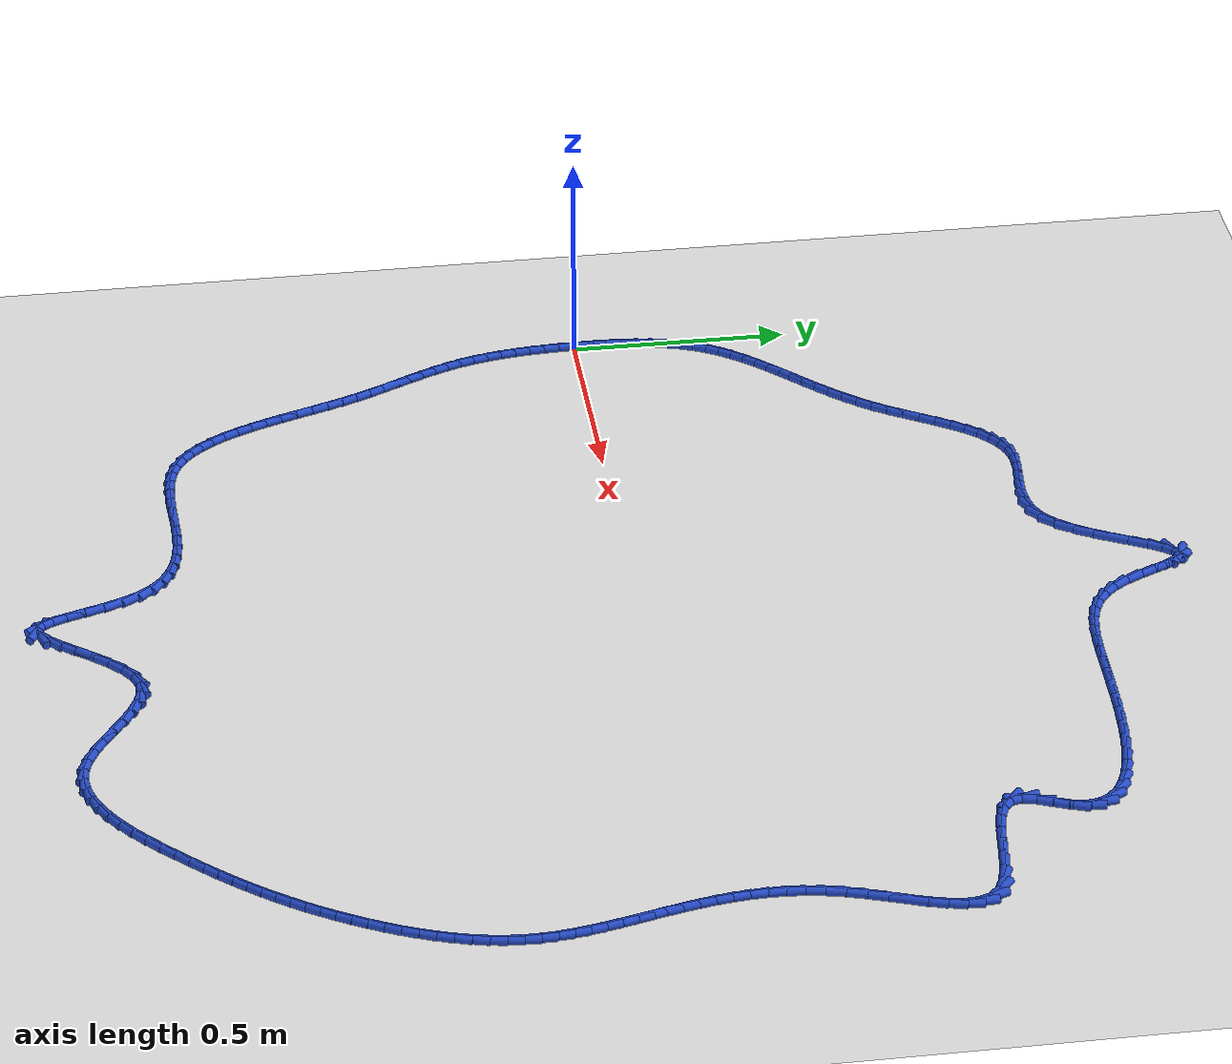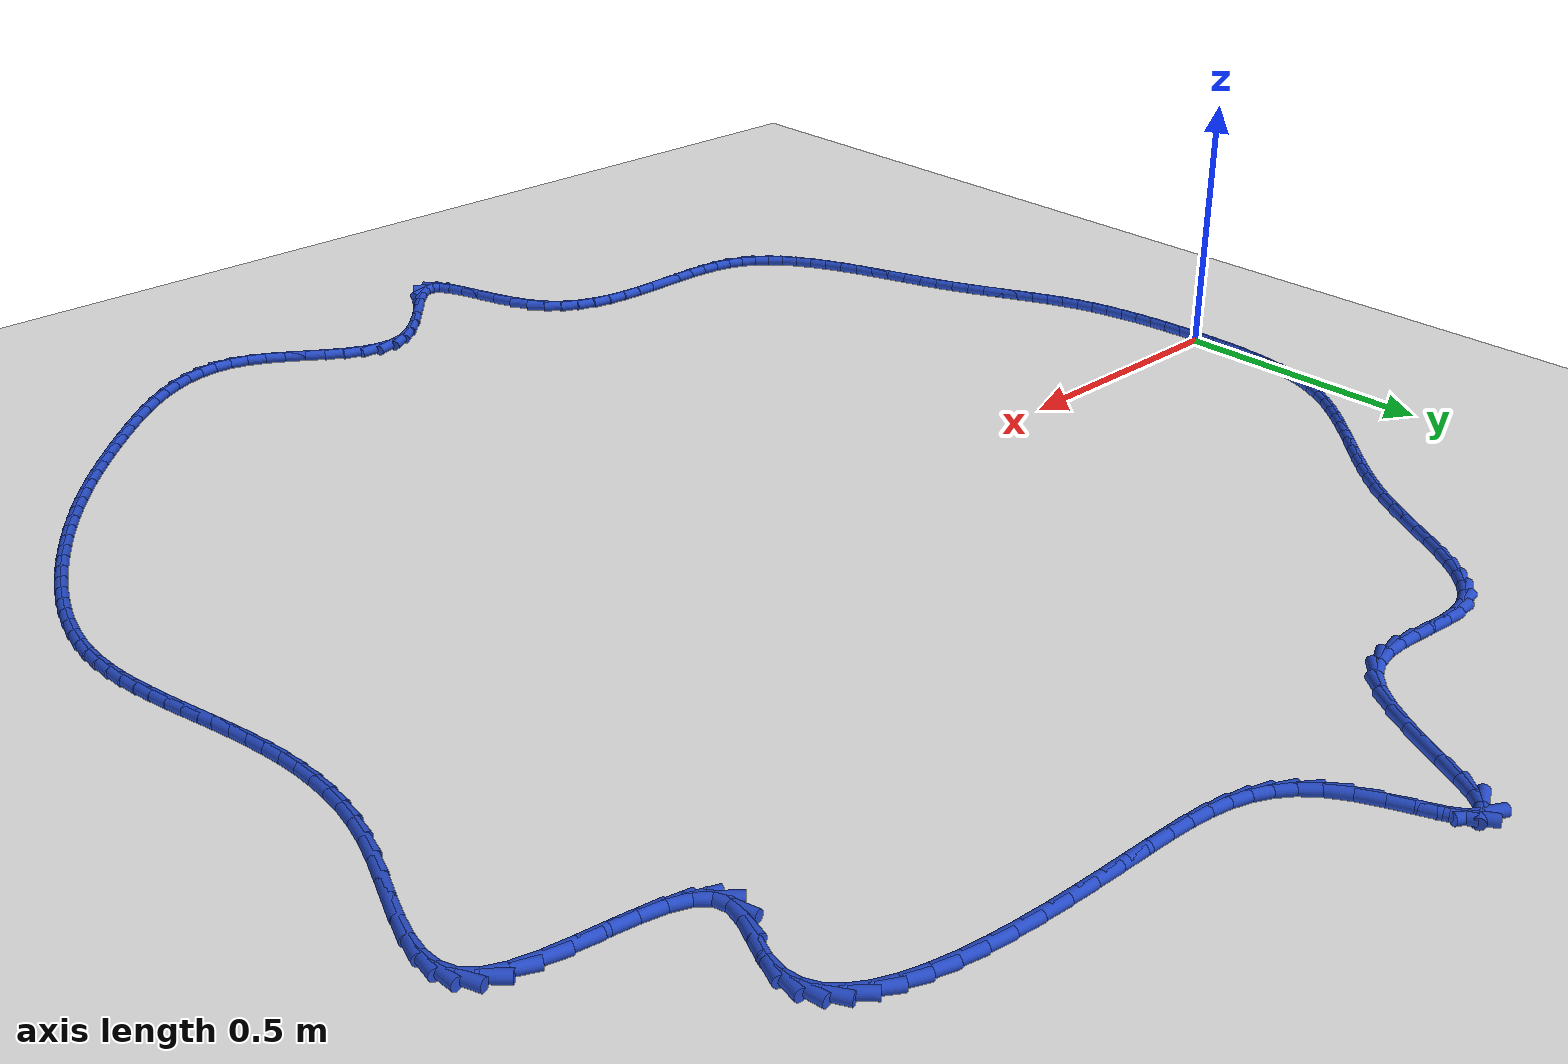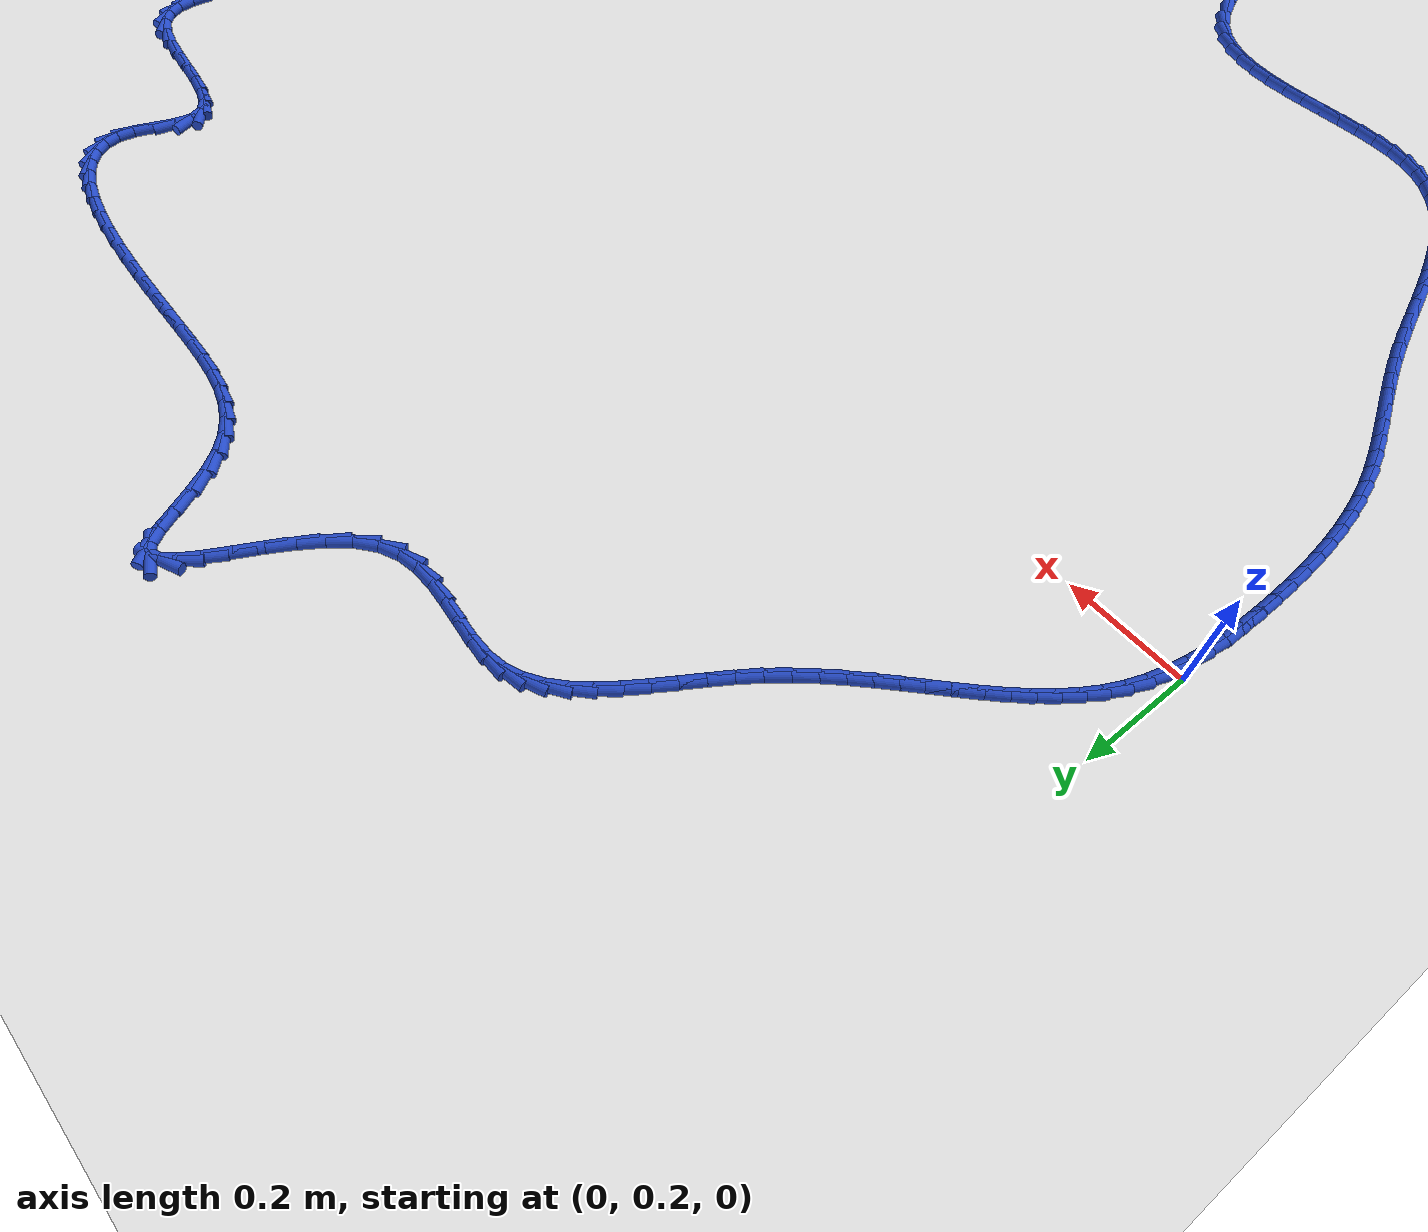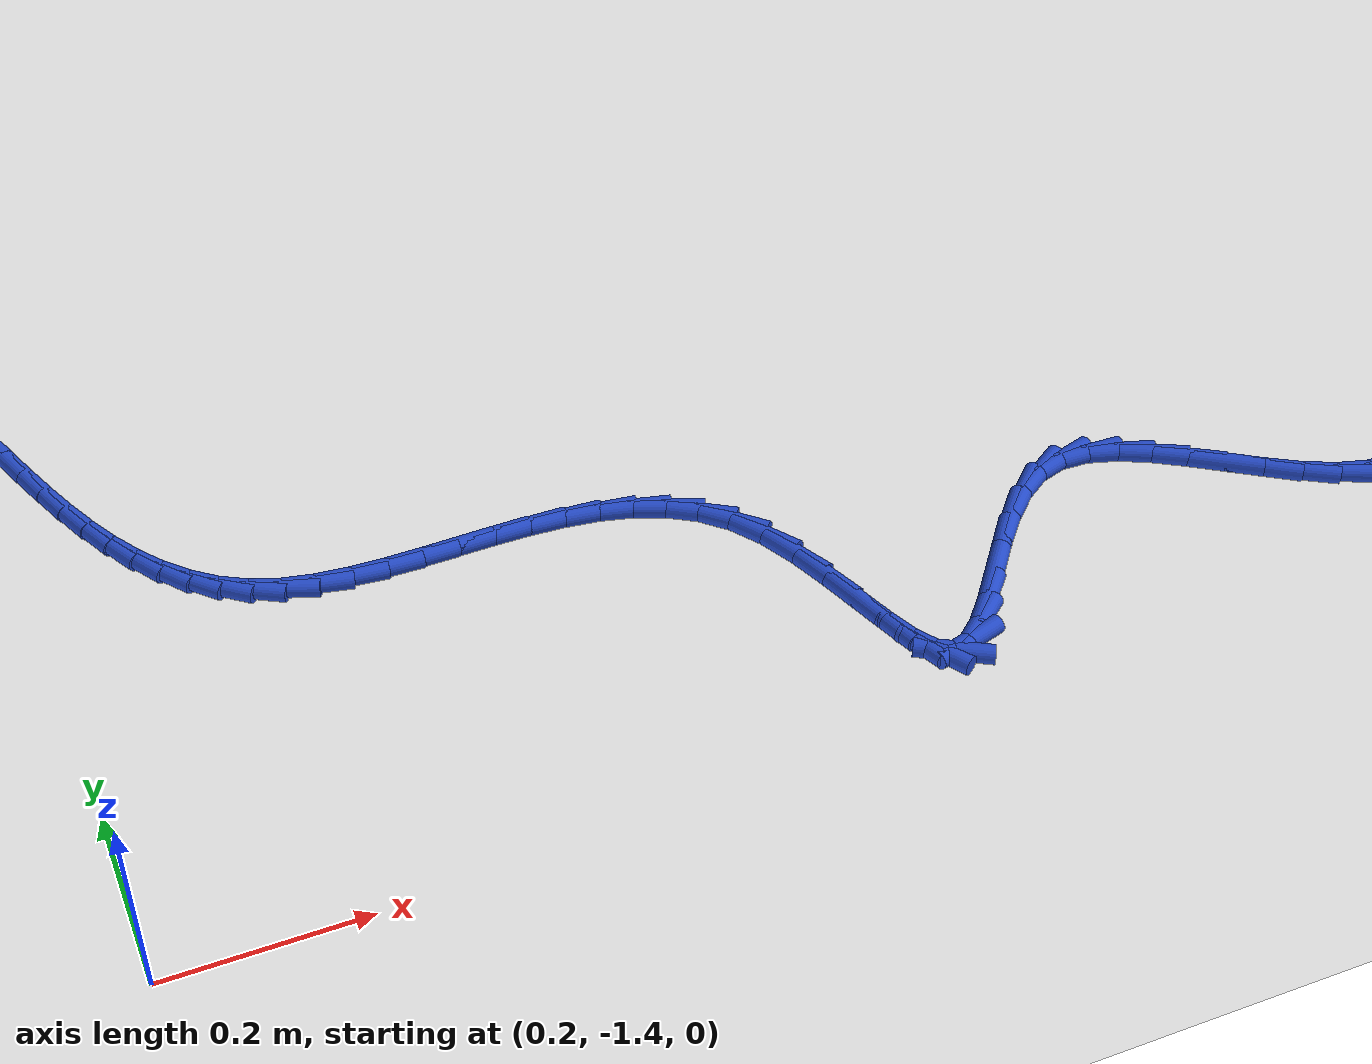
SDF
<sdf version="1.6">
 <world name="default">
  <light name="sun" type="directional">
   <pose>0 0 10 0 -0 0</pose>
   <diffuse>0.8 0.8 0.8 1</diffuse>
   <specular>0.2 0.2 0.2 1</specular>
   <attenuation>
    <range>1000</range>
    <constant>0.9</constant>
    <linear>0.01</linear>
    <quadratic>0.001</quadratic>
   </attenuation>
   <direction>-0.5 0.1 -0.9</direction>
  </light>
  <model name="ground_plane">
   <static>1</static>
   <link name="link">
    <collision name="collision">
     <geometry><plane><normal>0 0 1</normal><size>100 100</size></plane></geometry>
     <surface><friction><ode><mu>100</mu><mu2>50</mu2></ode></friction></surface>
    </collision>
    <visual name="visual">
     <cast_shadows>0</cast_shadows>
     <geometry><plane><normal>0 0 1</normal><size>100 100</size></plane></geometry>
     <material>
      <script><uri>file://media/materials/scripts/gazebo.material</uri><name>Gazebo/WhiteGlow</name></script>
     </material>
    </visual>
   </link>
  </model>
  <gravity>0 0 -9.8</gravity>
  <magnetic_field>6e-06 2.3e-05 -4.2e-05</magnetic_field>
  <atmosphere type="adiabatic"/>
  <physics name="default_physics" default="0" type="ode">
   <max_step_size>0.001</max_step_size>
   <real_time_factor>1</real_time_factor>
   <real_time_update_rate>1000</real_time_update_rate>
  </physics>
  <scene><ambient>0.4 0.4 0.4 1</ambient><background>0.7 0.7 0.7 1</background><shadows>1</shadows></scene>
  <spherical_coordinates>
   <surface_model>EARTH_WGS84</surface_model>
   <latitude_deg>0</latitude_deg>
   <longitude_deg>0</longitude_deg>
   <elevation>0</elevation>
   <heading_deg>0</heading_deg>
  </spherical_coordinates>
  <model name="line">
   <link name="link_0">
    <pose>1.3010426069826053e-18 8.326672684688674e-17 0.01 0 1.57 -1.565366141619233</pose>
    <collision name="collision">
     <geometry><cylinder><radius>0.01</radius><length>0.08</length></cylinder></geometry>
    </collision>
    <visual name="visual">
     <material>
      <script><name>Gazebo/Blue</name><uri>file://media/materials/scripts/gazebo.material</uri></script>
     </material>
     <geometry><cylinder><radius>0.01</radius><length>0.08</length></cylinder></geometry>
    </visual>
   </link>
   <link name="link_1">
    <pose>-0.00019903912547662052 0.03665384562116599 0.01 0 1.57 1.5497522830583188</pose>
    <collision name="collision">
     <geometry><cylinder><radius>0.01</radius><length>0.08</length></cylinder></geometry>
    </collision>
    <visual name="visual">
     <material>
      <script><name>Gazebo/Blue</name><uri>file://media/materials/scripts/gazebo.material</uri></script>
     </material>
     <geometry><cylinder><radius>0.01</radius><length>0.08</length></cylinder></geometry>
    </visual>
   </link>
   <link name="link_2">
    <pose>0.0005720877665993205 0.0732919113241402 0.01 0 1.57 1.5162058321206462</pose>
    <collision name="collision">
     <geometry><cylinder><radius>0.01</radius><length>0.08</length></cylinder></geometry>
    </collision>
    <visual name="visual">
     <material>
      <script><name>Gazebo/Blue</name><uri>file://media/materials/scripts/gazebo.material</uri></script>
     </material>
     <geometry><cylinder><radius>0.01</radius><length>0.08</length></cylinder></geometry>
    </visual>
   </link>
   <link name="link_3">
    <pose>0.002559975060530085 0.1096702624953205 0.01 0 1.57 1.4748888044440365</pose>
    <collision name="collision">
     <geometry><cylinder><radius>0.01</radius><length>0.08</length></cylinder></geometry>
    </collision>
    <visual name="visual">
     <material>
      <script><name>Gazebo/Blue</name><uri>file://media/materials/scripts/gazebo.material</uri></script>
     </material>
     <geometry><cylinder><radius>0.01</radius><length>0.08</length></cylinder></geometry>
    </visual>
   </link>
   <link name="link_4">
    <pose>0.006011217140617942 0.1455449645211047 0.01 0 1.57 1.4249111777290846</pose>
    <collision name="collision">
     <geometry><cylinder><radius>0.01</radius><length>0.08</length></cylinder></geometry>
    </collision>
    <visual name="visual">
     <material>
      <script><name>Gazebo/Blue</name><uri>file://media/materials/scripts/gazebo.material</uri></script>
     </material>
     <geometry><cylinder><radius>0.01</radius><length>0.08</length></cylinder></geometry>
    </visual>
   </link>
   <link name="link_5">
    <pose>0.011172408391165156 0.1806720827878907 0.01 0 1.57 1.3652282323918097</pose>
    <collision name="collision">
     <geometry><cylinder><radius>0.01</radius><length>0.08</length></cylinder></geometry>
    </collision>
    <visual name="visual">
     <material>
      <script><name>Gazebo/Blue</name><uri>file://media/materials/scripts/gazebo.material</uri></script>
     </material>
     <geometry><cylinder><radius>0.01</radius><length>0.08</length></cylinder></geometry>
    </visual>
   </link>
   <link name="link_6">
    <pose>0.018290143196473988 0.21480768268207634 0.01 0 1.57 1.294722816720855</pose>
    <collision name="collision">
     <geometry><cylinder><radius>0.01</radius><length>0.08</length></cylinder></geometry>
    </collision>
    <visual name="visual">
     <material>
      <script><name>Gazebo/Blue</name><uri>file://media/materials/scripts/gazebo.material</uri></script>
     </material>
     <geometry><cylinder><radius>0.01</radius><length>0.08</length></cylinder></geometry>
    </visual>
   </link>
   <link name="link_7">
    <pose>0.027611015940846702 0.24770782959005927 0.01 0 1.57 1.2123655410511154</pose>
    <collision name="collision">
     <geometry><cylinder><radius>0.01</radius><length>0.08</length></cylinder></geometry>
    </collision>
    <visual name="visual">
     <material>
      <script><name>Gazebo/Blue</name><uri>file://media/materials/scripts/gazebo.material</uri></script>
     </material>
     <geometry><cylinder><radius>0.01</radius><length>0.08</length></cylinder></geometry>
    </visual>
   </link>
   <link name="link_8">
    <pose>0.039381621008585575 0.27912858889823744 0.01 0 1.57 1.1202044283204897</pose>
    <collision name="collision">
     <geometry><cylinder><radius>0.01</radius><length>0.08</length></cylinder></geometry>
    </collision>
    <visual name="visual">
     <material>
      <script><name>Gazebo/Blue</name><uri>file://media/materials/scripts/gazebo.material</uri></script>
     </material>
     <geometry><cylinder><radius>0.01</radius><length>0.08</length></cylinder></geometry>
    </visual>
   </link>
   <link name="link_9">
    <pose>0.05377998950423215 0.3088904871146969 0.01 0 1.57 1.0331039443091243</pose>
    <collision name="collision">
     <geometry><cylinder><radius>0.01</radius><length>0.08</length></cylinder></geometry>
    </collision>
    <visual name="visual">
     <material>
      <script><name>Gazebo/Blue</name><uri>file://media/materials/scripts/gazebo.material</uri></script>
     </material>
     <geometry><cylinder><radius>0.01</radius><length>0.08</length></cylinder></geometry>
    </visual>
   </link>
   <link name="link_10">
    <pose>0.0706295364994129 0.33714745001503477 0.01 0 1.57 0.9575793137139381</pose>
    <collision name="collision">
     <geometry><cylinder><radius>0.01</radius><length>0.08</length></cylinder></geometry>
    </collision>
    <visual name="visual">
     <material>
      <script><name>Gazebo/Blue</name><uri>file://media/materials/scripts/gazebo.material</uri></script>
     </material>
     <geometry><cylinder><radius>0.01</radius><length>0.08</length></cylinder></geometry>
    </visual>
   </link>
   <link name="link_11">
    <pose>0.08963937092457887 0.3641608705511814 0.01 0 1.57 0.894789049111524</pose>
    <collision name="collision">
     <geometry><cylinder><radius>0.01</radius><length>0.08</length></cylinder></geometry>
    </collision>
    <visual name="visual">
     <material>
      <script><name>Gazebo/Blue</name><uri>file://media/materials/scripts/gazebo.material</uri></script>
     </material>
     <geometry><cylinder><radius>0.01</radius><length>0.08</length></cylinder></geometry>
    </visual>
   </link>
   <link name="link_12">
    <pose>0.11051854609933574 0.39019219395870175 0.01 0 1.57 0.8450553062116164</pose>
    <collision name="collision">
     <geometry><cylinder><radius>0.01</radius><length>0.08</length></cylinder></geometry>
    </collision>
    <visual name="visual">
     <material>
      <script><name>Gazebo/Blue</name><uri>file://media/materials/scripts/gazebo.material</uri></script>
     </material>
     <geometry><cylinder><radius>0.01</radius><length>0.08</length></cylinder></geometry>
    </visual>
   </link>
   <link name="link_13">
    <pose>0.1329761153432892 0.415502865473161 0.01 0 1.57 0.8081623031246014</pose>
    <collision name="collision">
     <geometry><cylinder><radius>0.01</radius><length>0.08</length></cylinder></geometry>
    </collision>
    <visual name="visual">
     <material>
      <script><name>Gazebo/Blue</name><uri>file://media/materials/scripts/gazebo.material</uri></script>
     </material>
     <geometry><cylinder><radius>0.01</radius><length>0.08</length></cylinder></geometry>
    </visual>
   </link>
   <link name="link_14">
    <pose>0.15672113197604493 0.4403543303301238 0.01 0 1.57 0.7836203838422565</pose>
    <collision name="collision">
     <geometry><cylinder><radius>0.01</radius><length>0.08</length></cylinder></geometry>
    </collision>
    <visual name="visual">
     <material>
      <script><name>Gazebo/Blue</name><uri>file://media/materials/scripts/gazebo.material</uri></script>
     </material>
     <geometry><cylinder><radius>0.01</radius><length>0.08</length></cylinder></geometry>
    </visual>
   </link>
   <link name="link_15">
    <pose>0.1814626493172087 0.4650080337651555 0.01 0 1.57 0.7708533505037601</pose>
    <collision name="collision">
     <geometry><cylinder><radius>0.01</radius><length>0.08</length></cylinder></geometry>
    </collision>
    <visual name="visual">
     <material>
      <script><name>Gazebo/Blue</name><uri>file://media/materials/scripts/gazebo.material</uri></script>
     </material>
     <geometry><cylinder><radius>0.01</radius><length>0.08</length></cylinder></geometry>
    </visual>
   </link>
   <link name="link_16">
    <pose>0.2069097206863861 0.48972542101382077 0.01 0 1.57 0.7693073143122566</pose>
    <collision name="collision">
     <geometry><cylinder><radius>0.01</radius><length>0.08</length></cylinder></geometry>
    </collision>
    <visual name="visual">
     <material>
      <script><name>Gazebo/Blue</name><uri>file://media/materials/scripts/gazebo.material</uri></script>
     </material>
     <geometry><cylinder><radius>0.01</radius><length>0.08</length></cylinder></geometry>
    </visual>
   </link>
   <link name="link_17">
    <pose>0.23277139940318298 0.5147679373116848 0.01 0 1.57 0.7784961566398637</pose>
    <collision name="collision">
     <geometry><cylinder><radius>0.01</radius><length>0.08</length></cylinder></geometry>
    </collision>
    <visual name="visual">
     <material>
      <script><name>Gazebo/Blue</name><uri>file://media/materials/scripts/gazebo.material</uri></script>
     </material>
     <geometry><cylinder><radius>0.01</radius><length>0.08</length></cylinder></geometry>
    </visual>
   </link>
   <link name="link_18">
    <pose>0.2587567387872048 0.5403970278943124 0.01 0 1.57 0.7980001288526365</pose>
    <collision name="collision">
     <geometry><cylinder><radius>0.01</radius><length>0.08</length></cylinder></geometry>
    </collision>
    <visual name="visual">
     <material>
      <script><name>Gazebo/Blue</name><uri>file://media/materials/scripts/gazebo.material</uri></script>
     </material>
     <geometry><cylinder><radius>0.01</radius><length>0.08</length></cylinder></geometry>
    </visual>
   </link>
   <link name="link_19">
    <pose>0.2845747921580574 0.5668741379972688 0.01 0 1.57 0.8274301596720719</pose>
    <collision name="collision">
     <geometry><cylinder><radius>0.01</radius><length>0.08</length></cylinder></geometry>
    </collision>
    <visual name="visual">
     <material>
      <script><name>Gazebo/Blue</name><uri>file://media/materials/scripts/gazebo.material</uri></script>
     </material>
     <geometry><cylinder><radius>0.01</radius><length>0.08</length></cylinder></geometry>
    </visual>
   </link>
   <link name="link_20">
    <pose>0.3099346128353465 0.5944607128561189 0.01 0 1.57 0.866366838404875</pose>
    <collision name="collision">
     <geometry><cylinder><radius>0.01</radius><length>0.08</length></cylinder></geometry>
    </collision>
    <visual name="visual">
     <material>
      <script><name>Gazebo/Blue</name><uri>file://media/materials/scripts/gazebo.material</uri></script>
     </material>
     <geometry><cylinder><radius>0.01</radius><length>0.08</length></cylinder></geometry>
    </visual>
   </link>
   <link name="link_21">
    <pose>0.3345452541386777 0.6234181977064275 0.01 0 1.57 0.9142823876673153</pose>
    <collision name="collision">
     <geometry><cylinder><radius>0.01</radius><length>0.08</length></cylinder></geometry>
    </collision>
    <visual name="visual">
     <material>
      <script><name>Gazebo/Blue</name><uri>file://media/materials/scripts/gazebo.material</uri></script>
     </material>
     <geometry><cylinder><radius>0.01</radius><length>0.08</length></cylinder></geometry>
    </visual>
   </link>
   <link name="link_22">
    <pose>0.3581157693876568 0.6540080377837598 0.01 0 1.57 0.9670866839030043</pose>
    <collision name="collision">
     <geometry><cylinder><radius>0.01</radius><length>0.08</length></cylinder></geometry>
    </collision>
    <visual name="visual">
     <material>
      <script><name>Gazebo/Blue</name><uri>file://media/materials/scripts/gazebo.material</uri></script>
     </material>
     <geometry><cylinder><radius>0.01</radius><length>0.08</length></cylinder></geometry>
    </visual>
   </link>
   <link name="link_23">
    <pose>0.3804327791958674 0.6863704502758111 0.01 0 1.57 1.0047887589611968</pose>
    <collision name="collision">
     <geometry><cylinder><radius>0.01</radius><length>0.08</length></cylinder></geometry>
    </collision>
    <visual name="visual">
     <material>
      <script><name>Gazebo/Blue</name><uri>file://media/materials/scripts/gazebo.material</uri></script>
     </material>
     <geometry><cylinder><radius>0.01</radius><length>0.08</length></cylinder></geometry>
    </visual>
   </link>
   <link name="link_24">
    <pose>0.4017478536597574 0.7199189940678494 0.01 0 1.57 1.0215269439173364</pose>
    <collision name="collision">
     <geometry><cylinder><radius>0.01</radius><length>0.08</length></cylinder></geometry>
    </collision>
    <visual name="visual">
     <material>
      <script><name>Gazebo/Blue</name><uri>file://media/materials/scripts/gazebo.material</uri></script>
     </material>
     <geometry><cylinder><radius>0.01</radius><length>0.08</length></cylinder></geometry>
    </visual>
   </link>
   <link name="link_25">
    <pose>0.4224850214187674 0.7537976967590401 0.01 0 1.57 1.0178594747072323</pose>
    <collision name="collision">
     <geometry><cylinder><radius>0.01</radius><length>0.08</length></cylinder></geometry>
    </collision>
    <visual name="visual">
     <material>
      <script><name>Gazebo/Blue</name><uri>file://media/materials/scripts/gazebo.material</uri></script>
     </material>
     <geometry><cylinder><radius>0.01</radius><length>0.08</length></cylinder></geometry>
    </visual>
   </link>
   <link name="link_26">
    <pose>0.44306859448594665 0.7871501430707885 0.01 0 1.57 0.9927970162421363</pose>
    <collision name="collision">
     <geometry><cylinder><radius>0.01</radius><length>0.08</length></cylinder></geometry>
    </collision>
    <visual name="visual">
     <material>
      <script><name>Gazebo/Blue</name><uri>file://media/materials/scripts/gazebo.material</uri></script>
     </material>
     <geometry><cylinder><radius>0.01</radius><length>0.08</length></cylinder></geometry>
    </visual>
   </link>
   <link name="link_27">
    <pose>0.4639228848743438 0.8191199177244993 0.01 0 1.57 0.9436078346301174</pose>
    <collision name="collision">
     <geometry><cylinder><radius>0.01</radius><length>0.08</length></cylinder></geometry>
    </collision>
    <visual name="visual">
     <material>
      <script><name>Gazebo/Blue</name><uri>file://media/materials/scripts/gazebo.material</uri></script>
     </material>
     <geometry><cylinder><radius>0.01</radius><length>0.08</length></cylinder></geometry>
    </visual>
   </link>
   <link name="link_28">
    <pose>0.4854722045970078 0.848850605441578 0.01 0 1.57 0.8656758754591497</pose>
    <collision name="collision">
     <geometry><cylinder><radius>0.01</radius><length>0.08</length></cylinder></geometry>
    </collision>
    <visual name="visual">
     <material>
      <script><name>Gazebo/Blue</name><uri>file://media/materials/scripts/gazebo.material</uri></script>
     </material>
     <geometry><cylinder><radius>0.01</radius><length>0.08</length></cylinder></geometry>
    </visual>
   </link>
   <link name="link_29">
    <pose>0.5081408656669879 0.8754857909434296 0.01 0 1.57 0.7528043701032412</pose>
    <collision name="collision">
     <geometry><cylinder><radius>0.01</radius><length>0.08</length></cylinder></geometry>
    </collision>
    <visual name="visual">
     <material>
      <script><name>Gazebo/Blue</name><uri>file://media/materials/scripts/gazebo.material</uri></script>
     </material>
     <geometry><cylinder><radius>0.01</radius><length>0.08</length></cylinder></geometry>
    </visual>
   </link>
   <link name="link_30">
    <pose>0.5323531800973331 0.8981690589514598 0.01 0 1.57 0.5990638222572501</pose>
    <collision name="collision">
     <geometry><cylinder><radius>0.01</radius><length>0.08</length></cylinder></geometry>
    </collision>
    <visual name="visual">
     <material>
      <script><name>Gazebo/Blue</name><uri>file://media/materials/scripts/gazebo.material</uri></script>
     </material>
     <geometry><cylinder><radius>0.01</radius><length>0.08</length></cylinder></geometry>
    </visual>
   </link>
   <link name="link_31">
    <pose>0.5585334599010925 0.9160439941870733 0.01 0 1.57 0.40385069944111107</pose>
    <collision name="collision">
     <geometry><cylinder><radius>0.01</radius><length>0.08</length></cylinder></geometry>
    </collision>
    <visual name="visual">
     <material>
      <script><name>Gazebo/Blue</name><uri>file://media/materials/scripts/gazebo.material</uri></script>
     </material>
     <geometry><cylinder><radius>0.01</radius><length>0.08</length></cylinder></geometry>
    </visual>
   </link>
   <link name="link_32">
    <pose>0.5871060170913148 0.9282541813716751 0.01 0 1.57 0.18158814374336443</pose>
    <collision name="collision">
     <geometry><cylinder><radius>0.01</radius><length>0.08</length></cylinder></geometry>
    </collision>
    <visual name="visual">
     <material>
      <script><name>Gazebo/Blue</name><uri>file://media/materials/scripts/gazebo.material</uri></script>
     </material>
     <geometry><cylinder><radius>0.01</radius><length>0.08</length></cylinder></geometry>
    </visual>
   </link>
   <link name="link_33">
    <pose>0.618468696822709 0.9340127060964651 0.01 0 1.57 0.002265711379368067</pose>
    <collision name="collision">
     <geometry><cylinder><radius>0.01</radius><length>0.08</length></cylinder></geometry>
    </collision>
    <visual name="visual">
     <material>
      <script><name>Gazebo/Blue</name><uri>file://media/materials/scripts/gazebo.material</uri></script>
     </material>
     <geometry><cylinder><radius>0.01</radius><length>0.08</length></cylinder></geometry>
    </visual>
   </link>
   <link name="link_34">
    <pose>0.6524264214297649 0.9340896446311782 0.01 0 1.57 -0.09199547964538214</pose>
    <collision name="collision">
     <geometry><cylinder><radius>0.01</radius><length>0.08</length></cylinder></geometry>
    </collision>
    <visual name="visual">
     <material>
      <script><name>Gazebo/Blue</name><uri>file://media/materials/scripts/gazebo.material</uri></script>
     </material>
     <geometry><cylinder><radius>0.01</radius><length>0.08</length></cylinder></geometry>
    </visual>
   </link>
   <link name="link_35">
    <pose>0.6881998456381658 0.9307893356987048 0.01 0 1.57 -0.11658881026703487</pose>
    <collision name="collision">
     <geometry><cylinder><radius>0.01</radius><length>0.08</length></cylinder></geometry>
    </collision>
    <visual name="visual">
     <material>
      <script><name>Gazebo/Blue</name><uri>file://media/materials/scripts/gazebo.material</uri></script>
     </material>
     <geometry><cylinder><radius>0.01</radius><length>0.08</length></cylinder></geometry>
    </visual>
   </link>
   <link name="link_36">
    <pose>0.7249848884748822 0.9264810729385159 0.01 0 1.57 -0.07949466341857395</pose>
    <collision name="collision">
     <geometry><cylinder><radius>0.01</radius><length>0.08</length></cylinder></geometry>
    </collision>
    <visual name="visual">
     <material>
      <script><name>Gazebo/Blue</name><uri>file://media/materials/scripts/gazebo.material</uri></script>
     </material>
     <geometry><cylinder><radius>0.01</radius><length>0.08</length></cylinder></geometry>
    </visual>
   </link>
   <link name="link_37">
    <pose>0.7619774689668835 0.9235341499900798 0.01 0 1.57 0.02152952549953946</pose>
    <collision name="collision">
     <geometry><cylinder><radius>0.01</radius><length>0.08</length></cylinder></geometry>
    </collision>
    <visual name="visual">
     <material>
      <script><name>Gazebo/Blue</name><uri>file://media/materials/scripts/gazebo.material</uri></script>
     </material>
     <geometry><cylinder><radius>0.01</radius><length>0.08</length></cylinder></geometry>
    </visual>
   </link>
   <link name="link_38">
    <pose>0.798373506141139 0.9243178604928668 0.01 0 1.57 0.19422157574366936</pose>
    <collision name="collision">
     <geometry><cylinder><radius>0.01</radius><length>0.08</length></cylinder></geometry>
    </collision>
    <visual name="visual">
     <material>
      <script><name>Gazebo/Blue</name><uri>file://media/materials/scripts/gazebo.material</uri></script>
     </material>
     <geometry><cylinder><radius>0.01</radius><length>0.08</length></cylinder></geometry>
    </visual>
   </link>
   <link name="link_39">
    <pose>0.8333689190246194 0.9312014980863462 0.01 0 1.57 0.4378917725070002</pose>
    <collision name="collision">
     <geometry><cylinder><radius>0.01</radius><length>0.08</length></cylinder></geometry>
    </collision>
    <visual name="visual">
     <material>
      <script><name>Gazebo/Blue</name><uri>file://media/materials/scripts/gazebo.material</uri></script>
     </material>
     <geometry><cylinder><radius>0.01</radius><length>0.08</length></cylinder></geometry>
    </visual>
   </link>
   <link name="link_40">
    <pose>0.8661596266442937 0.9465543564099878 0.01 0 1.57 0.7033480801861134</pose>
    <collision name="collision">
     <geometry><cylinder><radius>0.01</radius><length>0.08</length></cylinder></geometry>
    </collision>
    <visual name="visual">
     <material>
      <script><name>Gazebo/Blue</name><uri>file://media/materials/scripts/gazebo.material</uri></script>
     </material>
     <geometry><cylinder><radius>0.01</radius><length>0.08</length></cylinder></geometry>
    </visual>
   </link>
   <link name="link_41">
    <pose>0.8961046343801986 0.9719485603083635 0.01 0 1.57 0.8886059507664142</pose>
    <collision name="collision">
     <geometry><cylinder><radius>0.01</radius><length>0.08</length></cylinder></geometry>
    </collision>
    <visual name="visual">
     <material>
      <script><name>Gazebo/Blue</name><uri>file://media/materials/scripts/gazebo.material</uri></script>
     </material>
     <geometry><cylinder><radius>0.01</radius><length>0.08</length></cylinder></geometry>
    </visual>
   </link>
   <link name="link_42">
    <pose>0.9232877596463951 1.0054133413990733 0.01 0 1.57 1.0012127696572173</pose>
    <collision name="collision">
     <geometry><cylinder><radius>0.01</radius><length>0.08</length></cylinder></geometry>
    </collision>
    <visual name="visual">
     <material>
      <script><name>Gazebo/Blue</name><uri>file://media/materials/scripts/gazebo.material</uri></script>
     </material>
     <geometry><cylinder><radius>0.01</radius><length>0.08</length></cylinder></geometry>
    </visual>
   </link>
   <link name="link_43">
    <pose>0.9479941078253828 1.0439940323761654 0.01 0 1.57 1.065945739766662</pose>
    <collision name="collision">
     <geometry><cylinder><radius>0.01</radius><length>0.08</length></cylinder></geometry>
    </collision>
    <visual name="visual">
     <material>
      <script><name>Gazebo/Blue</name><uri>file://media/materials/scripts/gazebo.material</uri></script>
     </material>
     <geometry><cylinder><radius>0.01</radius><length>0.08</length></cylinder></geometry>
    </visual>
   </link>
   <link name="link_44">
    <pose>0.9705087921415044 1.0847359276026345 0.01 0 1.57 1.0945343477757163</pose>
    <collision name="collision">
     <geometry><cylinder><radius>0.01</radius><length>0.08</length></cylinder></geometry>
    </collision>
    <visual name="visual">
     <material>
      <script><name>Gazebo/Blue</name><uri>file://media/materials/scripts/gazebo.material</uri></script>
     </material>
     <geometry><cylinder><radius>0.01</radius><length>0.08</length></cylinder></geometry>
    </visual>
   </link>
   <link name="link_45">
    <pose>0.9911169258191018 1.1246843214414763 0.01 0 1.57 1.087747907198237</pose>
    <collision name="collision">
     <geometry><cylinder><radius>0.01</radius><length>0.08</length></cylinder></geometry>
    </collision>
    <visual name="visual">
     <material>
      <script><name>Gazebo/Blue</name><uri>file://media/materials/scripts/gazebo.material</uri></script>
     </material>
     <geometry><cylinder><radius>0.01</radius><length>0.08</length></cylinder></geometry>
    </visual>
   </link>
   <link name="link_46">
    <pose>1.010103622082517 1.1608845082556851 0.01 0 1.57 1.0315740176226684</pose>
    <collision name="collision">
     <geometry><cylinder><radius>0.01</radius><length>0.08</length></cylinder></geometry>
    </collision>
    <visual name="visual">
     <material>
      <script><name>Gazebo/Blue</name><uri>file://media/materials/scripts/gazebo.material</uri></script>
     </material>
     <geometry><cylinder><radius>0.01</radius><length>0.08</length></cylinder></geometry>
    </visual>
   </link>
   <link name="link_47">
    <pose>1.0277539941560923 1.190381782408256 0.01 0 1.57 0.8740945821807543</pose>
    <collision name="collision">
     <geometry><cylinder><radius>0.01</radius><length>0.08</length></cylinder></geometry>
    </collision>
    <visual name="visual">
     <material>
      <script><name>Gazebo/Blue</name><uri>file://media/materials/scripts/gazebo.material</uri></script>
     </material>
     <geometry><cylinder><radius>0.01</radius><length>0.08</length></cylinder></geometry>
    </visual>
   </link>
   <link name="link_48">
    <pose>1.0443531552641694 1.2102214382621843 0.01 0 1.57 0.4282220409804943</pose>
    <collision name="collision">
     <geometry><cylinder><radius>0.01</radius><length>0.08</length></cylinder></geometry>
    </collision>
    <visual name="visual">
     <material>
      <script><name>Gazebo/Blue</name><uri>file://media/materials/scripts/gazebo.material</uri></script>
     </material>
     <geometry><cylinder><radius>0.01</radius><length>0.08</length></cylinder></geometry>
    </visual>
   </link>
   <link name="link_49">
    <pose>1.0601862186310909 1.217448770180465 0.01 0 1.57 -0.4913779624600538</pose>
    <collision name="collision">
     <geometry><cylinder><radius>0.01</radius><length>0.08</length></cylinder></geometry>
    </collision>
    <visual name="visual">
     <material>
      <script><name>Gazebo/Blue</name><uri>file://media/materials/scripts/gazebo.material</uri></script>
     </material>
     <geometry><cylinder><radius>0.01</radius><length>0.08</length></cylinder></geometry>
    </visual>
   </link>
   <link name="link_50">
    <pose>1.0755437644178132 1.2092300344785571 0.01 0 1.57 -0.9808681145622187</pose>
    <collision name="collision">
     <geometry><cylinder><radius>0.01</radius><length>0.08</length></cylinder></geometry>
    </collision>
    <visual name="visual">
     <material>
      <script><name>Gazebo/Blue</name><uri>file://media/materials/scripts/gazebo.material</uri></script>
     </material>
     <geometry><cylinder><radius>0.01</radius><length>0.08</length></cylinder></geometry>
    </visual>
   </link>
   <link name="link_51">
    <pose>1.0908787071843848 1.1863233136169105 0.01 0 1.57 -1.1172891857659133</pose>
    <collision name="collision">
     <geometry><cylinder><radius>0.01</radius><length>0.08</length></cylinder></geometry>
    </collision>
    <visual name="visual">
     <material>
      <script><name>Gazebo/Blue</name><uri>file://media/materials/scripts/gazebo.material</uri></script>
     </material>
     <geometry><cylinder><radius>0.01</radius><length>0.08</length></cylinder></geometry>
    </visual>
   </link>
   <link name="link_52">
    <pose>1.1068296771240524 1.1535958515805331 0.01 0 1.57 -1.1399647260535226</pose>
    <collision name="collision">
     <geometry><cylinder><radius>0.01</radius><length>0.08</length></cylinder></geometry>
    </collision>
    <visual name="visual">
     <material>
      <script><name>Gazebo/Blue</name><uri>file://media/materials/scripts/gazebo.material</uri></script>
     </material>
     <geometry><cylinder><radius>0.01</radius><length>0.08</length></cylinder></geometry>
    </visual>
   </link>
   <link name="link_53">
    <pose>1.124045474171045 1.1161399089975614 0.01 0 1.57 -1.0946465420658669</pose>
    <collision name="collision">
     <geometry><cylinder><radius>0.01</radius><length>0.08</length></cylinder></geometry>
    </collision>
    <visual name="visual">
     <material>
      <script><name>Gazebo/Blue</name><uri>file://media/materials/scripts/gazebo.material</uri></script>
     </material>
     <geometry><cylinder><radius>0.01</radius><length>0.08</length></cylinder></geometry>
    </visual>
   </link>
   <link name="link_54">
    <pose>1.143174898259593 1.079047746496133 0.01 0 1.57 -0.9745898468676989</pose>
    <collision name="collision">
     <geometry><cylinder><radius>0.01</radius><length>0.08</length></cylinder></geometry>
    </collision>
    <visual name="visual">
     <material>
      <script><name>Gazebo/Blue</name><uri>file://media/materials/scripts/gazebo.material</uri></script>
     </material>
     <geometry><cylinder><radius>0.01</radius><length>0.08</length></cylinder></geometry>
    </visual>
   </link>
   <link name="link_55">
    <pose>1.1648346772784155 1.0471285763058709 0.01 0 1.57 -0.803147359494654</pose>
    <collision name="collision">
     <geometry><cylinder><radius>0.01</radius><length>0.08</length></cylinder></geometry>
    </collision>
    <visual name="visual">
     <material>
      <script><name>Gazebo/Blue</name><uri>file://media/materials/scripts/gazebo.material</uri></script>
     </material>
     <geometry><cylinder><radius>0.01</radius><length>0.08</length></cylinder></geometry>
    </visual>
   </link>
   <link name="link_56">
    <pose>1.1892595998306017 1.0218208464468965 0.01 0 1.57 -0.6217404524278279</pose>
    <collision name="collision">
     <geometry><cylinder><radius>0.01</radius><length>0.08</length></cylinder></geometry>
    </collision>
    <visual name="visual">
     <material>
      <script><name>Gazebo/Blue</name><uri>file://media/materials/scripts/gazebo.material</uri></script>
     </material>
     <geometry><cylinder><radius>0.01</radius><length>0.08</length></cylinder></geometry>
    </visual>
   </link>
   <link name="link_57">
    <pose>1.2164336502059765 1.0023495583666935 0.01 0 1.57 -0.4501037662684579</pose>
    <collision name="collision">
     <geometry><cylinder><radius>0.01</radius><length>0.08</length></cylinder></geometry>
    </collision>
    <visual name="visual">
     <material>
      <script><name>Gazebo/Blue</name><uri>file://media/materials/scripts/gazebo.material</uri></script>
     </material>
     <geometry><cylinder><radius>0.01</radius><length>0.08</length></cylinder></geometry>
    </visual>
   </link>
   <link name="link_58">
    <pose>1.2463364308023117 0.987901041594314 0.01 0 1.57 -0.30423761250381726</pose>
    <collision name="collision">
     <geometry><cylinder><radius>0.01</radius><length>0.08</length></cylinder></geometry>
    </collision>
    <visual name="visual">
     <material>
      <script><name>Gazebo/Blue</name><uri>file://media/materials/scripts/gazebo.material</uri></script>
     </material>
     <geometry><cylinder><radius>0.01</radius><length>0.08</length></cylinder></geometry>
    </visual>
   </link>
   <link name="link_59">
    <pose>1.2789475440173814 0.9776616256588098 0.01 0 1.57 -0.191509705843064</pose>
    <collision name="collision">
     <geometry><cylinder><radius>0.01</radius><length>0.08</length></cylinder></geometry>
    </collision>
    <visual name="visual">
     <material>
      <script><name>Gazebo/Blue</name><uri>file://media/materials/scripts/gazebo.material</uri></script>
     </material>
     <geometry><cylinder><radius>0.01</radius><length>0.08</length></cylinder></geometry>
    </visual>
   </link>
   <link name="link_60">
    <pose>1.3142465922489568 0.970817640089233 0.01 0 1.57 -0.11179447274638207</pose>
    <collision name="collision">
     <geometry><cylinder><radius>0.01</radius><length>0.08</length></cylinder></geometry>
    </collision>
    <visual name="visual">
     <material>
      <script><name>Gazebo/Blue</name><uri>file://media/materials/scripts/gazebo.material</uri></script>
     </material>
     <geometry><cylinder><radius>0.01</radius><length>0.08</length></cylinder></geometry>
    </visual>
   </link>
   <link name="link_61">
    <pose>1.352213177894812 0.9665554144146358 0.01 0 1.57 -0.06133413996050201</pose>
    <collision name="collision">
     <geometry><cylinder><radius>0.01</radius><length>0.08</length></cylinder></geometry>
    </collision>
    <visual name="visual">
     <material>
      <script><name>Gazebo/Blue</name><uri>file://media/materials/scripts/gazebo.material</uri></script>
     </material>
     <geometry><cylinder><radius>0.01</radius><length>0.08</length></cylinder></geometry>
    </visual>
   </link>
   <link name="link_62">
    <pose>1.3928269033527187 0.9640612781640698 0.01 0 1.57 -0.03559320967096441</pose>
    <collision name="collision">
     <geometry><cylinder><radius>0.01</radius><length>0.08</length></cylinder></geometry>
    </collision>
    <visual name="visual">
     <material>
      <script><name>Gazebo/Blue</name><uri>file://media/materials/scripts/gazebo.material</uri></script>
     </material>
     <geometry><cylinder><radius>0.01</radius><length>0.08</length></cylinder></geometry>
    </visual>
   </link>
   <link name="link_63">
    <pose>1.4360673710204508 0.9625215608665874 0.01 0 1.57 -0.02899583581267326</pose>
    <collision name="collision">
     <geometry><cylinder><radius>0.01</radius><length>0.08</length></cylinder></geometry>
    </collision>
    <visual name="visual">
     <material>
      <script><name>Gazebo/Blue</name><uri>file://media/materials/scripts/gazebo.material</uri></script>
     </material>
     <geometry><cylinder><radius>0.01</radius><length>0.08</length></cylinder></geometry>
    </visual>
   </link>
   <link name="link_64">
    <pose>1.481798892920301 0.9611951654191987 0.01 0 1.57 -0.03181918137966791</pose>
    <collision name="collision">
     <geometry><cylinder><radius>0.01</radius><length>0.08</length></cylinder></geometry>
    </collision>
    <visual name="visual">
     <material>
      <script><name>Gazebo/Blue</name><uri>file://media/materials/scripts/gazebo.material</uri></script>
     </material>
     <geometry><cylinder><radius>0.01</radius><length>0.08</length></cylinder></geometry>
    </visual>
   </link>
   <link name="link_65">
    <pose>1.5293443825058572 0.9596817960856887 0.01 0 1.57 -0.0412079252949086</pose>
    <collision name="collision">
     <geometry><cylinder><radius>0.01</radius><length>0.08</length></cylinder></geometry>
    </collision>
    <visual name="visual">
     <material>
      <script><name>Gazebo/Blue</name><uri>file://media/materials/scripts/gazebo.material</uri></script>
     </material>
     <geometry><cylinder><radius>0.01</radius><length>0.08</length></cylinder></geometry>
    </visual>
   </link>
   <link name="link_66">
    <pose>1.577867972358921 0.9576811070396687 0.01 0 1.57 -0.057233134213137825</pose>
    <collision name="collision">
     <geometry><cylinder><radius>0.01</radius><length>0.08</length></cylinder></geometry>
    </collision>
    <visual name="visual">
     <material>
      <script><name>Gazebo/Blue</name><uri>file://media/materials/scripts/gazebo.material</uri></script>
     </material>
     <geometry><cylinder><radius>0.01</radius><length>0.08</length></cylinder></geometry>
    </visual>
   </link>
   <link name="link_67">
    <pose>1.62653377438693 0.9548927654689172 0.01 0 1.57 -0.08062855713013198</pose>
    <collision name="collision">
     <geometry><cylinder><radius>0.01</radius><length>0.08</length></cylinder></geometry>
    </collision>
    <visual name="visual">
     <material>
      <script><name>Gazebo/Blue</name><uri>file://media/materials/scripts/gazebo.material</uri></script>
     </material>
     <geometry><cylinder><radius>0.01</radius><length>0.08</length></cylinder></geometry>
    </visual>
   </link>
   <link name="link_68">
    <pose>1.674505900497321 0.9510164385612124 0.01 0 1.57 -0.11287635162903507</pose>
    <collision name="collision">
     <geometry><cylinder><radius>0.01</radius><length>0.08</length></cylinder></geometry>
    </collision>
    <visual name="visual">
     <material>
      <script><name>Gazebo/Blue</name><uri>file://media/materials/scripts/gazebo.material</uri></script>
     </material>
     <geometry><cylinder><radius>0.01</radius><length>0.08</length></cylinder></geometry>
    </visual>
   </link>
   <link name="link_69">
    <pose>1.7209484625975309 0.9457517935043331 0.01 0 1.57 -0.15646357779761397</pose>
    <collision name="collision">
     <geometry><cylinder><radius>0.01</radius><length>0.08</length></cylinder></geometry>
    </collision>
    <visual name="visual">
     <material>
      <script><name>Gazebo/Blue</name><uri>file://media/materials/scripts/gazebo.material</uri></script>
     </material>
     <geometry><cylinder><radius>0.01</radius><length>0.08</length></cylinder></geometry>
    </visual>
   </link>
   <link name="link_70">
    <pose>1.7650255725949981 0.9387984974860576 0.01 0 1.57 -0.21537416284267957</pose>
    <collision name="collision">
     <geometry><cylinder><radius>0.01</radius><length>0.08</length></cylinder></geometry>
    </collision>
    <visual name="visual">
     <material>
      <script><name>Gazebo/Blue</name><uri>file://media/materials/scripts/gazebo.material</uri></script>
     </material>
     <geometry><cylinder><radius>0.01</radius><length>0.08</length></cylinder></geometry>
    </visual>
   </link>
   <link name="link_71">
    <pose>1.805901342397158 0.9298562176941642 0.01 0 1.57 -0.295934327029937</pose>
    <collision name="collision">
     <geometry><cylinder><radius>0.01</radius><length>0.08</length></cylinder></geometry>
    </collision>
    <visual name="visual">
     <material>
      <script><name>Gazebo/Blue</name><uri>file://media/materials/scripts/gazebo.material</uri></script>
     </material>
     <geometry><cylinder><radius>0.01</radius><length>0.08</length></cylinder></geometry>
    </visual>
   </link>
   <link name="link_72">
    <pose>1.8427398839114497 0.9186246213164315 0.01 0 1.57 -0.40810585983567776</pose>
    <collision name="collision">
     <geometry><cylinder><radius>0.01</radius><length>0.08</length></cylinder></geometry>
    </collision>
    <visual name="visual">
     <material>
      <script><name>Gazebo/Blue</name><uri>file://media/materials/scripts/gazebo.material</uri></script>
     </material>
     <geometry><cylinder><radius>0.01</radius><length>0.08</length></cylinder></geometry>
    </visual>
   </link>
   <link name="link_73">
    <pose>1.8747053090453087 0.904803375540638 0.01 0 1.57 -0.5667996050922918</pose>
    <collision name="collision">
     <geometry><cylinder><radius>0.01</radius><length>0.08</length></cylinder></geometry>
    </collision>
    <visual name="visual">
     <material>
      <script><name>Gazebo/Blue</name><uri>file://media/materials/scripts/gazebo.material</uri></script>
     </material>
     <geometry><cylinder><radius>0.01</radius><length>0.08</length></cylinder></geometry>
    </visual>
   </link>
   <link name="link_74">
    <pose>1.9009617297061736 0.8880921475545621 0.01 0 1.57 -0.7901948996929119</pose>
    <collision name="collision">
     <geometry><cylinder><radius>0.01</radius><length>0.08</length></cylinder></geometry>
    </collision>
    <visual name="visual">
     <material>
      <script><name>Gazebo/Blue</name><uri>file://media/materials/scripts/gazebo.material</uri></script>
     </material>
     <geometry><cylinder><radius>0.01</radius><length>0.08</length></cylinder></geometry>
    </visual>
   </link>
   <link name="link_75">
    <pose>1.9206732578014813 0.8681906045459826 0.01 0 1.57 -1.085680287643788</pose>
    <collision name="collision">
     <geometry><cylinder><radius>0.01</radius><length>0.08</length></cylinder></geometry>
    </collision>
    <visual name="visual">
     <material>
      <script><name>Gazebo/Blue</name><uri>file://media/materials/scripts/gazebo.material</uri></script>
     </material>
     <geometry><cylinder><radius>0.01</radius><length>0.08</length></cylinder></geometry>
    </visual>
   </link>
   <link name="link_76">
    <pose>1.9330040052386683 0.8447984137026773 0.01 0 1.57 -1.4205897400191951</pose>
    <collision name="collision">
     <geometry><cylinder><radius>0.01</radius><length>0.08</length></cylinder></geometry>
    </collision>
    <visual name="visual">
     <material>
      <script><name>Gazebo/Blue</name><uri>file://media/materials/scripts/gazebo.material</uri></script>
     </material>
     <geometry><cylinder><radius>0.01</radius><length>0.08</length></cylinder></geometry>
    </visual>
   </link>
   <link name="link_77">
    <pose>1.9371180839251725 0.8176152422124251 0.01 0 1.57 1.4141911830292309</pose>
    <collision name="collision">
     <geometry><cylinder><radius>0.01</radius><length>0.08</length></cylinder></geometry>
    </collision>
    <visual name="visual">
     <material>
      <script><name>Gazebo/Blue</name><uri>file://media/materials/scripts/gazebo.material</uri></script>
     </material>
     <geometry><cylinder><radius>0.01</radius><length>0.08</length></cylinder></geometry>
    </visual>
   </link>
   <link name="link_78">
    <pose>1.9321799264135198 0.7863409078249171 0.01 0 1.57 1.2125164082445472</pose>
    <collision name="collision">
     <geometry><cylinder><radius>0.01</radius><length>0.08</length></cylinder></geometry>
    </collision>
    <visual name="visual">
     <material>
      <script><name>Gazebo/Blue</name><uri>file://media/materials/scripts/gazebo.material</uri></script>
     </material>
     <geometry><cylinder><radius>0.01</radius><length>0.08</length></cylinder></geometry>
    </visual>
   </link>
   <link name="link_79">
    <pose>1.919139128137144 0.7515134682872507 0.01 0 1.57 1.1852236447687536</pose>
    <collision name="collision">
     <geometry><cylinder><radius>0.01</radius><length>0.08</length></cylinder></geometry>
    </collision>
    <visual name="visual">
     <material>
      <script><name>Gazebo/Blue</name><uri>file://media/materials/scripts/gazebo.material</uri></script>
     </material>
     <geometry><cylinder><radius>0.01</radius><length>0.08</length></cylinder></geometry>
    </visual>
   </link>
   <link name="link_80">
    <pose>1.9049175260118971 0.716475303427305 0.01 0 1.57 1.343838760808624</pose>
    <collision name="collision">
     <geometry><cylinder><radius>0.01</radius><length>0.08</length></cylinder></geometry>
    </collision>
    <visual name="visual">
     <material>
      <script><name>Gazebo/Blue</name><uri>file://media/materials/scripts/gazebo.material</uri></script>
     </material>
     <geometry><cylinder><radius>0.01</radius><length>0.08</length></cylinder></geometry>
    </visual>
   </link>
   <link name="link_81">
    <pose>1.8976844244732238 0.6851545531632973 0.01 0 1.57 -1.3001773517629749</pose>
    <collision name="collision">
     <geometry><cylinder><radius>0.01</radius><length>0.08</length></cylinder></geometry>
    </collision>
    <visual name="visual">
     <material>
      <script><name>Gazebo/Blue</name><uri>file://media/materials/scripts/gazebo.material</uri></script>
     </material>
     <geometry><cylinder><radius>0.01</radius><length>0.08</length></cylinder></geometry>
    </visual>
   </link>
   <link name="link_82">
    <pose>1.9044153847363772 0.6608922512643634 0.01 0 1.57 -0.707640985548467</pose>
    <collision name="collision">
     <geometry><cylinder><radius>0.01</radius><length>0.08</length></cylinder></geometry>
    </collision>
    <visual name="visual">
     <material>
      <script><name>Gazebo/Blue</name><uri>file://media/materials/scripts/gazebo.material</uri></script>
     </material>
     <geometry><cylinder><radius>0.01</radius><length>0.08</length></cylinder></geometry>
    </visual>
   </link>
   <link name="link_83">
    <pose>1.9248062977462892 0.6434491479791191 0.01 0 1.57 -0.37525118180244893</pose>
    <collision name="collision">
     <geometry><cylinder><radius>0.01</radius><length>0.08</length></cylinder></geometry>
    </collision>
    <visual name="visual">
     <material>
      <script><name>Gazebo/Blue</name><uri>file://media/materials/scripts/gazebo.material</uri></script>
     </material>
     <geometry><cylinder><radius>0.01</radius><length>0.08</length></cylinder></geometry>
    </visual>
   </link>
   <link name="link_84">
    <pose>1.9558092839322263 0.6312365538155698 0.01 0 1.57 -0.21876477993075943</pose>
    <collision name="collision">
     <geometry><cylinder><radius>0.01</radius><length>0.08</length></cylinder></geometry>
    </collision>
    <visual name="visual">
     <material>
      <script><name>Gazebo/Blue</name><uri>file://media/materials/scripts/gazebo.material</uri></script>
     </material>
     <geometry><cylinder><radius>0.01</radius><length>0.08</length></cylinder></geometry>
    </visual>
   </link>
   <link name="link_85">
    <pose>1.994371438790331 0.6226633079218096 0.01 0 1.57 -0.15036099702550895</pose>
    <collision name="collision">
     <geometry><cylinder><radius>0.01</radius><length>0.08</length></cylinder></geometry>
    </collision>
    <visual name="visual">
     <material>
      <script><name>Gazebo/Blue</name><uri>file://media/materials/scripts/gazebo.material</uri></script>
     </material>
     <geometry><cylinder><radius>0.01</radius><length>0.08</length></cylinder></geometry>
    </visual>
   </link>
   <link name="link_86">
    <pose>2.0374398578167408 0.6161382494459328 0.01 0 1.57 -0.1354589205520616</pose>
    <collision name="collision">
     <geometry><cylinder><radius>0.01</radius><length>0.08</length></cylinder></geometry>
    </collision>
    <visual name="visual">
     <material>
      <script><name>Gazebo/Blue</name><uri>file://media/materials/scripts/gazebo.material</uri></script>
     </material>
     <geometry><cylinder><radius>0.01</radius><length>0.08</length></cylinder></geometry>
    </visual>
   </link>
   <link name="link_87">
    <pose>2.081961636507597 0.610070217536033 0.01 0 1.57 -0.16624699301828738</pose>
    <collision name="collision">
     <geometry><cylinder><radius>0.01</radius><length>0.08</length></cylinder></geometry>
    </collision>
    <visual name="visual">
     <material>
      <script><name>Gazebo/Blue</name><uri>file://media/materials/scripts/gazebo.material</uri></script>
     </material>
     <geometry><cylinder><radius>0.01</radius><length>0.08</length></cylinder></geometry>
    </visual>
   </link>
   <link name="link_88">
    <pose>2.124883870359039 0.6028680513402048 0.01 0 1.57 -0.25381280462859684</pose>
    <collision name="collision">
     <geometry><cylinder><radius>0.01</radius><length>0.08</length></cylinder></geometry>
    </collision>
    <visual name="visual">
     <material>
      <script><name>Gazebo/Blue</name><uri>file://media/materials/scripts/gazebo.material</uri></script>
     </material>
     <geometry><cylinder><radius>0.01</radius><length>0.08</length></cylinder></geometry>
    </visual>
   </link>
   <link name="link_89">
    <pose>2.1631536548672075 0.5929405900065421 0.01 0 1.57 -0.4361035689409837</pose>
    <collision name="collision">
     <geometry><cylinder><radius>0.01</radius><length>0.08</length></cylinder></geometry>
    </collision>
    <visual name="visual">
     <material>
      <script><name>Gazebo/Blue</name><uri>file://media/materials/scripts/gazebo.material</uri></script>
     </material>
     <geometry><cylinder><radius>0.01</radius><length>0.08</length></cylinder></geometry>
    </visual>
   </link>
   <link name="link_90">
    <pose>2.1937180855282414 0.5786966726831391 0.01 0 1.57 -0.7797357250943816</pose>
    <collision name="collision">
     <geometry><cylinder><radius>0.01</radius><length>0.08</length></cylinder></geometry>
    </collision>
    <visual name="visual">
     <material>
      <script><name>Gazebo/Blue</name><uri>file://media/materials/scripts/gazebo.material</uri></script>
     </material>
     <geometry><cylinder><radius>0.01</radius><length>0.08</length></cylinder></geometry>
    </visual>
   </link>
   <link name="link_91">
    <pose>2.2139035362966473 0.5587385349374249 0.01 0 1.57 -1.194065106549389</pose>
    <collision name="collision">
     <geometry><cylinder><radius>0.01</radius><length>0.08</length></cylinder></geometry>
    </collision>
    <visual name="visual">
     <material>
      <script><name>Gazebo/Blue</name><uri>file://media/materials/scripts/gazebo.material</uri></script>
     </material>
     <geometry><cylinder><radius>0.01</radius><length>0.08</length></cylinder></geometry>
    </visual>
   </link>
   <link name="link_92">
    <pose>2.2240127809233825 0.5331860969045834 0.01 0 1.57 -1.5134267150380483</pose>
    <collision name="collision">
     <geometry><cylinder><radius>0.01</radius><length>0.08</length></cylinder></geometry>
    </collision>
    <visual name="visual">
     <material>
      <script><name>Gazebo/Blue</name><uri>file://media/materials/scripts/gazebo.material</uri></script>
     </material>
     <geometry><cylinder><radius>0.01</radius><length>0.08</length></cylinder></geometry>
    </visual>
   </link>
   <link name="link_93">
    <pose>2.225753587221357 0.5028756938358568 0.01 0 1.57 1.4282728691432591</pose>
    <collision name="collision">
     <geometry><cylinder><radius>0.01</radius><length>0.08</length></cylinder></geometry>
    </collision>
    <visual name="visual">
     <material>
      <script><name>Gazebo/Blue</name><uri>file://media/materials/scripts/gazebo.material</uri></script>
     </material>
     <geometry><cylinder><radius>0.01</radius><length>0.08</length></cylinder></geometry>
    </visual>
   </link>
   <link name="link_94">
    <pose>2.2208420213793105 0.4686478923753775 0.01 0 1.57 1.3126990277508228</pose>
    <collision name="collision">
     <geometry><cylinder><radius>0.01</radius><length>0.08</length></cylinder></geometry>
    </collision>
    <visual name="visual">
     <material>
      <script><name>Gazebo/Blue</name><uri>file://media/materials/scripts/gazebo.material</uri></script>
     </material>
     <geometry><cylinder><radius>0.01</radius><length>0.08</length></cylinder></geometry>
    </visual>
   </link>
   <link name="link_95">
    <pose>2.210994149585984 0.43134325916727695 0.01 0 1.57 1.2516014778433917</pose>
    <collision name="collision">
     <geometry><cylinder><radius>0.01</radius><length>0.08</length></cylinder></geometry>
    </collision>
    <visual name="visual">
     <material>
      <script><name>Gazebo/Blue</name><uri>file://media/materials/scripts/gazebo.material</uri></script>
     </material>
     <geometry><cylinder><radius>0.01</radius><length>0.08</length></cylinder></geometry>
    </visual>
   </link>
   <link name="link_96">
    <pose>2.1979260380301184 0.3918023608556877 0.01 0 1.57 1.2288111155275985</pose>
    <collision name="collision">
     <geometry><cylinder><radius>0.01</radius><length>0.08</length></cylinder></geometry>
    </collision>
    <visual name="visual">
     <material>
      <script><name>Gazebo/Blue</name><uri>file://media/materials/scripts/gazebo.material</uri></script>
     </material>
     <geometry><cylinder><radius>0.01</radius><length>0.08</length></cylinder></geometry>
    </visual>
   </link>
   <link name="link_97">
    <pose>2.183353752900452 0.35086576408474107 0.01 0 1.57 1.2375978457063055</pose>
    <collision name="collision">
     <geometry><cylinder><radius>0.01</radius><length>0.08</length></cylinder></geometry>
    </collision>
    <visual name="visual">
     <material>
      <script><name>Gazebo/Blue</name><uri>file://media/materials/scripts/gazebo.material</uri></script>
     </material>
     <geometry><cylinder><radius>0.01</radius><length>0.08</length></cylinder></geometry>
    </visual>
   </link>
   <link name="link_98">
    <pose>2.1689933603857265 0.3093740354985688 0.01 0 1.57 1.2777672646779485</pose>
    <collision name="collision">
     <geometry><cylinder><radius>0.01</radius><length>0.08</length></cylinder></geometry>
    </collision>
    <visual name="visual">
     <material>
      <script><name>Gazebo/Blue</name><uri>file://media/materials/scripts/gazebo.material</uri></script>
     </material>
     <geometry><cylinder><radius>0.01</radius><length>0.08</length></cylinder></geometry>
    </visual>
   </link>
   <link name="link_99">
    <pose>2.1565608040812525 0.2681676866795718 0.01 0 1.57 1.3460673625649646</pose>
    <collision name="collision">
     <geometry><cylinder><radius>0.01</radius><length>0.08</length></cylinder></geometry>
    </collision>
    <visual name="visual">
     <material>
      <script><name>Gazebo/Blue</name><uri>file://media/materials/scripts/gazebo.material</uri></script>
     </material>
     <geometry><cylinder><radius>0.01</radius><length>0.08</length></cylinder></geometry>
    </visual>
   </link>
   <link name="link_100">
    <pose>2.147356103537456 0.2279004206817361 0.01 0 1.57 1.4186722724269851</pose>
    <collision name="collision">
     <geometry><cylinder><radius>0.01</radius><length>0.08</length></cylinder></geometry>
    </collision>
    <visual name="visual">
     <material>
      <script><name>Gazebo/Blue</name><uri>file://media/materials/scripts/gazebo.material</uri></script>
     </material>
     <geometry><cylinder><radius>0.01</radius><length>0.08</length></cylinder></geometry>
    </visual>
   </link>
   <link name="link_101">
    <pose>2.1413343709057804 0.18862188754709408 0.01 0 1.57 1.488738456251134</pose>
    <collision name="collision">
     <geometry><cylinder><radius>0.01</radius><length>0.08</length></cylinder></geometry>
    </collision>
    <visual name="visual">
     <material>
      <script><name>Gazebo/Blue</name><uri>file://media/materials/scripts/gazebo.material</uri></script>
     </material>
     <geometry><cylinder><radius>0.01</radius><length>0.08</length></cylinder></geometry>
    </visual>
   </link>
   <link name="link_102">
    <pose>2.1381793807626672 0.15025986849640402 0.01 0 1.57 1.5546860535242888</pose>
    <collision name="collision">
     <geometry><cylinder><radius>0.01</radius><length>0.08</length></cylinder></geometry>
    </collision>
    <visual name="visual">
     <material>
      <script><name>Gazebo/Blue</name><uri>file://media/materials/scripts/gazebo.material</uri></script>
     </material>
     <geometry><cylinder><radius>0.01</radius><length>0.08</length></cylinder></geometry>
    </visual>
   </link>
   <link name="link_103">
    <pose>2.1375749076845603 0.11274214475042633 0.01 0 1.57 -1.526471320292968</pose>
    <collision name="collision">
     <geometry><cylinder><radius>0.01</radius><length>0.08</length></cylinder></geometry>
    </collision>
    <visual name="visual">
     <material>
      <script><name>Gazebo/Blue</name><uri>file://media/materials/scripts/gazebo.material</uri></script>
     </material>
     <geometry><cylinder><radius>0.01</radius><length>0.08</length></cylinder></geometry>
    </visual>
   </link>
   <link name="link_104">
    <pose>2.139204726247904 0.07599649752991948 0.01 0 1.57 -1.4726851803526793</pose>
    <collision name="collision">
     <geometry><cylinder><radius>0.01</radius><length>0.08</length></cylinder></geometry>
    </collision>
    <visual name="visual">
     <material>
      <script><name>Gazebo/Blue</name><uri>file://media/materials/scripts/gazebo.material</uri></script>
     </material>
     <geometry><cylinder><radius>0.01</radius><length>0.08</length></cylinder></geometry>
    </visual>
   </link>
   <link name="link_105">
    <pose>2.142752611029142 0.039950708055643804 0.01 0 1.57 -1.4264101966500768</pose>
    <collision name="collision">
     <geometry><cylinder><radius>0.01</radius><length>0.08</length></cylinder></geometry>
    </collision>
    <visual name="visual">
     <material>
      <script><name>Gazebo/Blue</name><uri>file://media/materials/scripts/gazebo.material</uri></script>
     </material>
     <geometry><cylinder><radius>0.01</radius><length>0.08</length></cylinder></geometry>
    </visual>
   </link>
   <link name="link_106">
    <pose>2.147902336604717 0.004532557548357843 0.01 0 1.57 -1.3882602018610741</pose>
    <collision name="collision">
     <geometry><cylinder><radius>0.01</radius><length>0.08</length></cylinder></geometry>
    </collision>
    <visual name="visual">
     <material>
      <script><name>Gazebo/Blue</name><uri>file://media/materials/scripts/gazebo.material</uri></script>
     </material>
     <geometry><cylinder><radius>0.01</radius><length>0.08</length></cylinder></geometry>
    </visual>
   </link>
   <link name="link_107">
    <pose>2.154337677551073 -0.03033017277117803 0.01 0 1.57 -1.3586550955291756</pose>
    <collision name="collision">
     <geometry><cylinder><radius>0.01</radius><length>0.08</length></cylinder></geometry>
    </collision>
    <visual name="visual">
     <material>
      <script><name>Gazebo/Blue</name><uri>file://media/materials/scripts/gazebo.material</uri></script>
     </material>
     <geometry><cylinder><radius>0.01</radius><length>0.08</length></cylinder></geometry>
    </visual>
   </link>
   <link name="link_108">
    <pose>2.1617424084446553 -0.06470970168220531 0.01 0 1.57 -1.337885024137112</pose>
    <collision name="collision">
     <geometry><cylinder><radius>0.01</radius><length>0.08</length></cylinder></geometry>
    </collision>
    <visual name="visual">
     <material>
      <script><name>Gazebo/Blue</name><uri>file://media/materials/scripts/gazebo.material</uri></script>
     </material>
     <geometry><cylinder><radius>0.01</radius><length>0.08</length></cylinder></geometry>
    </visual>
   </link>
   <link name="link_109">
    <pose>2.1698003038619045 -0.0986782479639637 0.01 0 1.57 -1.32617063379561</pose>
    <collision name="collision">
     <geometry><cylinder><radius>0.01</radius><length>0.08</length></cylinder></geometry>
    </collision>
    <visual name="visual">
     <material>
      <script><name>Gazebo/Blue</name><uri>file://media/materials/scripts/gazebo.material</uri></script>
     </material>
     <geometry><cylinder><radius>0.01</radius><length>0.08</length></cylinder></geometry>
    </visual>
   </link>
   <link name="link_110">
    <pose>2.1781951383792655 -0.13230803039569455 0.01 0 1.57 -1.3237103954781941</pose>
    <collision name="collision">
     <geometry><cylinder><radius>0.01</radius><length>0.08</length></cylinder></geometry>
    </collision>
    <visual name="visual">
     <material>
      <script><name>Gazebo/Blue</name><uri>file://media/materials/scripts/gazebo.material</uri></script>
     </material>
     <geometry><cylinder><radius>0.01</radius><length>0.08</length></cylinder></geometry>
    </visual>
   </link>
   <link name="link_111">
    <pose>2.1866106865731822 -0.1656712677566377 0.01 0 1.57 -1.3307095735899024</pose>
    <collision name="collision">
     <geometry><cylinder><radius>0.01</radius><length>0.08</length></cylinder></geometry>
    </collision>
    <visual name="visual">
     <material>
      <script><name>Gazebo/Blue</name><uri>file://media/materials/scripts/gazebo.material</uri></script>
     </material>
     <geometry><cylinder><radius>0.01</radius><length>0.08</length></cylinder></geometry>
    </visual>
   </link>
   <link name="link_112">
    <pose>2.1947307230200983 -0.19884017882603408 0.01 0 1.57 -1.34738699696556</pose>
    <collision name="collision">
     <geometry><cylinder><radius>0.01</radius><length>0.08</length></cylinder></geometry>
    </collision>
    <visual name="visual">
     <material>
      <script><name>Gazebo/Blue</name><uri>file://media/materials/scripts/gazebo.material</uri></script>
     </material>
     <geometry><cylinder><radius>0.01</radius><length>0.08</length></cylinder></geometry>
    </visual>
   </link>
   <link name="link_113">
    <pose>2.2022390222964563 -0.23188698238312422 0.01 0 1.57 -1.3739558420042326</pose>
    <collision name="collision">
     <geometry><cylinder><radius>0.01</radius><length>0.08</length></cylinder></geometry>
    </collision>
    <visual name="visual">
     <material>
      <script><name>Gazebo/Blue</name><uri>file://media/materials/scripts/gazebo.material</uri></script>
     </material>
     <geometry><cylinder><radius>0.01</radius><length>0.08</length></cylinder></geometry>
    </visual>
   </link>
   <link name="link_114">
    <pose>2.2088193589787006 -0.26488389720714955 0.01 0 1.57 -1.4105743478422037</pose>
    <collision name="collision">
     <geometry><cylinder><radius>0.01</radius><length>0.08</length></cylinder></geometry>
    </collision>
    <visual name="visual">
     <material>
      <script><name>Gazebo/Blue</name><uri>file://media/materials/scripts/gazebo.material</uri></script>
     </material>
     <geometry><cylinder><radius>0.01</radius><length>0.08</length></cylinder></geometry>
    </visual>
   </link>
   <link name="link_115">
    <pose>2.2141555076432753 -0.297903142077349 0.01 0 1.57 -1.4572636209553493</pose>
    <collision name="collision">
     <geometry><cylinder><radius>0.01</radius><length>0.08</length></cylinder></geometry>
    </collision>
    <visual name="visual">
     <material>
      <script><name>Gazebo/Blue</name><uri>file://media/materials/scripts/gazebo.material</uri></script>
     </material>
     <geometry><cylinder><radius>0.01</radius><length>0.08</length></cylinder></geometry>
    </visual>
   </link>
   <link name="link_116">
    <pose>2.2179312428666234 -0.3310169357729641 0.01 0 1.57 -1.5137949116955085</pose>
    <collision name="collision">
     <geometry><cylinder><radius>0.01</radius><length>0.08</length></cylinder></geometry>
    </collision>
    <visual name="visual">
     <material>
      <script><name>Gazebo/Blue</name><uri>file://media/materials/scripts/gazebo.material</uri></script>
     </material>
     <geometry><cylinder><radius>0.01</radius><length>0.08</length></cylinder></geometry>
    </visual>
   </link>
   <link name="link_117">
    <pose>2.219830339225188 -0.3642974970732351 0.01 0 1.57 1.5620324731909199</pose>
    <collision name="collision">
     <geometry><cylinder><radius>0.01</radius><length>0.08</length></cylinder></geometry>
    </collision>
    <visual name="visual">
     <material>
      <script><name>Gazebo/Blue</name><uri>file://media/materials/scripts/gazebo.material</uri></script>
     </material>
     <geometry><cylinder><radius>0.01</radius><length>0.08</length></cylinder></geometry>
    </visual>
   </link>
   <link name="link_118">
    <pose>2.2195365712954125 -0.39781704475740354 0.01 0 1.57 1.4892906407734199</pose>
    <collision name="collision">
     <geometry><cylinder><radius>0.01</radius><length>0.08</length></cylinder></geometry>
    </collision>
    <visual name="visual">
     <material>
      <script><name>Gazebo/Blue</name><uri>file://media/materials/scripts/gazebo.material</uri></script>
     </material>
     <geometry><cylinder><radius>0.01</radius><length>0.08</length></cylinder></geometry>
    </visual>
   </link>
   <link name="link_119">
    <pose>2.2167743081750038 -0.43163239936782605 0.01 0 1.57 1.4197599168719934</pose>
    <collision name="collision">
     <geometry><cylinder><radius>0.01</radius><length>0.08</length></cylinder></geometry>
    </collision>
    <visual name="visual">
     <material>
      <script><name>Gazebo/Blue</name><uri>file://media/materials/scripts/gazebo.material</uri></script>
     </material>
     <geometry><cylinder><radius>0.01</radius><length>0.08</length></cylinder></geometry>
    </visual>
   </link>
   <link name="link_120">
    <pose>2.2115928548642048 -0.46567712737603023 0.01 0 1.57 1.3575254541519568</pose>
    <collision name="collision">
     <geometry><cylinder><radius>0.01</radius><length>0.08</length></cylinder></geometry>
    </collision>
    <visual name="visual">
     <material>
      <script><name>Gazebo/Blue</name><uri>file://media/materials/scripts/gazebo.material</uri></script>
     </material>
     <geometry><cylinder><radius>0.01</radius><length>0.08</length></cylinder></geometry>
    </visual>
   </link>
   <link name="link_121">
    <pose>2.2041975091937744 -0.49982562434866307 0.01 0 1.57 1.3019337084913316</pose>
    <collision name="collision">
     <geometry><cylinder><radius>0.01</radius><length>0.08</length></cylinder></geometry>
    </collision>
    <visual name="visual">
     <material>
      <script><name>Gazebo/Blue</name><uri>file://media/materials/scripts/gazebo.material</uri></script>
     </material>
     <geometry><cylinder><radius>0.01</radius><length>0.08</length></cylinder></geometry>
    </visual>
   </link>
   <link name="link_122">
    <pose>2.194794556087231 -0.5339519114302167 0.01 0 1.57 1.2522742930205133</pose>
    <collision name="collision">
     <geometry><cylinder><radius>0.01</radius><length>0.08</length></cylinder></geometry>
    </collision>
    <visual name="visual">
     <material>
      <script><name>Gazebo/Blue</name><uri>file://media/materials/scripts/gazebo.material</uri></script>
     </material>
     <geometry><cylinder><radius>0.01</radius><length>0.08</length></cylinder></geometry>
    </visual>
   </link>
   <link name="link_123">
    <pose>2.183590280468093 -0.5679300097651809 0.01 0 1.57 1.2078614237819887</pose>
    <collision name="collision">
     <geometry><cylinder><radius>0.01</radius><length>0.08</length></cylinder></geometry>
    </collision>
    <visual name="visual">
     <material>
      <script><name>Gazebo/Blue</name><uri>file://media/materials/scripts/gazebo.material</uri></script>
     </material>
     <geometry><cylinder><radius>0.01</radius><length>0.08</length></cylinder></geometry>
    </visual>
   </link>
   <link name="link_124">
    <pose>2.1707909672598804 -0.6016339404980482 0.01 0 1.57 1.1680623601713136</pose>
    <collision name="collision">
     <geometry><cylinder><radius>0.01</radius><length>0.08</length></cylinder></geometry>
    </collision>
    <visual name="visual">
     <material>
      <script><name>Gazebo/Blue</name><uri>file://media/materials/scripts/gazebo.material</uri></script>
     </material>
     <geometry><cylinder><radius>0.01</radius><length>0.08</length></cylinder></geometry>
    </visual>
   </link>
   <link name="link_125">
    <pose>2.15660290138611 -0.6349377247733099 0.01 0 1.57 1.1323095521492967</pose>
    <collision name="collision">
     <geometry><cylinder><radius>0.01</radius><length>0.08</length></cylinder></geometry>
    </collision>
    <visual name="visual">
     <material>
      <script><name>Gazebo/Blue</name><uri>file://media/materials/scripts/gazebo.material</uri></script>
     </material>
     <geometry><cylinder><radius>0.01</radius><length>0.08</length></cylinder></geometry>
    </visual>
   </link>
   <link name="link_126">
    <pose>2.141232367770301 -0.6677153837354586 0.01 0 1.57 1.1001030106544847</pose>
    <collision name="collision">
     <geometry><cylinder><radius>0.01</radius><length>0.08</length></cylinder></geometry>
    </collision>
    <visual name="visual">
     <material>
      <script><name>Gazebo/Blue</name><uri>file://media/materials/scripts/gazebo.material</uri></script>
     </material>
     <geometry><cylinder><radius>0.01</radius><length>0.08</length></cylinder></geometry>
    </visual>
   </link>
   <link name="link_127">
    <pose>2.124885651335972 -0.6998409385289837 0.01 0 1.57 1.0710073317774622</pose>
    <collision name="collision">
     <geometry><cylinder><radius>0.01</radius><length>0.08</length></cylinder></geometry>
    </collision>
    <visual name="visual">
     <material>
      <script><name>Gazebo/Blue</name><uri>file://media/materials/scripts/gazebo.material</uri></script>
     </material>
     <geometry><cylinder><radius>0.01</radius><length>0.08</length></cylinder></geometry>
    </visual>
   </link>
   <link name="link_128">
    <pose>2.1077690370066415 -0.7311884102983778 0.01 0 1.57 1.0445506364632249</pose>
    <collision name="collision">
     <geometry><cylinder><radius>0.01</radius><length>0.08</length></cylinder></geometry>
    </collision>
    <visual name="visual">
     <material>
      <script><name>Gazebo/Blue</name><uri>file://media/materials/scripts/gazebo.material</uri></script>
     </material>
     <geometry><cylinder><radius>0.01</radius><length>0.08</length></cylinder></geometry>
    </visual>
   </link>
   <link name="link_129">
    <pose>2.090080430172719 -0.7616395493683459 0.01 0 1.57 1.018941520231611</pose>
    <collision name="collision">
     <geometry><cylinder><radius>0.01</radius><length>0.08</length></cylinder></geometry>
    </collision>
    <visual name="visual">
     <material>
      <script><name>Gazebo/Blue</name><uri>file://media/materials/scripts/gazebo.material</uri></script>
     </material>
     <geometry><cylinder><radius>0.01</radius><length>0.08</length></cylinder></geometry>
    </visual>
   </link>
   <link name="link_130">
    <pose>2.0718783756213726 -0.7912046506021759 0.01 0 1.57 0.9930822187000926</pose>
    <collision name="collision">
     <geometry><cylinder><radius>0.01</radius><length>0.08</length></cylinder></geometry>
    </collision>
    <visual name="visual">
     <material>
      <script><name>Gazebo/Blue</name><uri>file://media/materials/scripts/gazebo.material</uri></script>
     </material>
     <geometry><cylinder><radius>0.01</radius><length>0.08</length></cylinder></geometry>
    </visual>
   </link>
   <link name="link_131">
    <pose>2.053106507097106 -0.8200000014221306 0.01 0 1.57 0.9672613384659791</pose>
    <collision name="collision">
     <geometry><cylinder><radius>0.01</radius><length>0.08</length></cylinder></geometry>
    </collision>
    <visual name="visual">
     <material>
      <script><name>Gazebo/Blue</name><uri>file://media/materials/scripts/gazebo.material</uri></script>
     </material>
     <geometry><cylinder><radius>0.01</radius><length>0.08</length></cylinder></geometry>
    </visual>
   </link>
   <link name="link_132">
    <pose>2.033705025837022 -0.8481450553538746 0.01 0 1.57 0.9418145961172039</pose>
    <collision name="collision">
     <geometry><cylinder><radius>0.01</radius><length>0.08</length></cylinder></geometry>
    </collision>
    <visual name="visual">
     <material>
      <script><name>Gazebo/Blue</name><uri>file://media/materials/scripts/gazebo.material</uri></script>
     </material>
     <geometry><cylinder><radius>0.01</radius><length>0.08</length></cylinder></geometry>
    </visual>
   </link>
   <link name="link_133">
    <pose>2.0136141330782182 -0.8757592659230738 0.01 0 1.57 0.9170700820153106</pose>
    <collision name="collision">
     <geometry><cylinder><radius>0.01</radius><length>0.08</length></cylinder></geometry>
    </collision>
    <visual name="visual">
     <material>
      <script><name>Gazebo/Blue</name><uri>file://media/materials/scripts/gazebo.material</uri></script>
     </material>
     <geometry><cylinder><radius>0.01</radius><length>0.08</length></cylinder></geometry>
    </visual>
   </link>
   <link name="link_134">
    <pose>1.9927740300577976 -0.9029620866553943 0.01 0 1.57 0.8933331657874355</pose>
    <collision name="collision">
     <geometry><cylinder><radius>0.01</radius><length>0.08</length></cylinder></geometry>
    </collision>
    <visual name="visual">
     <material>
      <script><name>Gazebo/Blue</name><uri>file://media/materials/scripts/gazebo.material</uri></script>
     </material>
     <geometry><cylinder><radius>0.01</radius><length>0.08</length></cylinder></geometry>
    </visual>
   </link>
   <link name="link_135">
    <pose>1.971124918012859 -0.9298729710765027 0.01 0 1.57 0.8708734557451395</pose>
    <collision name="collision">
     <geometry><cylinder><radius>0.01</radius><length>0.08</length></cylinder></geometry>
    </collision>
    <visual name="visual">
     <material>
      <script><name>Gazebo/Blue</name><uri>file://media/materials/scripts/gazebo.material</uri></script>
     </material>
     <geometry><cylinder><radius>0.01</radius><length>0.08</length></cylinder></geometry>
    </visual>
   </link>
   <link name="link_136">
    <pose>1.9486069981805043 -0.9566113727120634 0.01 0 1.57 0.8499149882618812</pose>
    <collision name="collision">
     <geometry><cylinder><radius>0.01</radius><length>0.08</length></cylinder></geometry>
    </collision>
    <visual name="visual">
     <material>
      <script><name>Gazebo/Blue</name><uri>file://media/materials/scripts/gazebo.material</uri></script>
     </material>
     <geometry><cylinder><radius>0.01</radius><length>0.08</length></cylinder></geometry>
    </visual>
   </link>
   <link name="link_137">
    <pose>1.9251604717978343 -0.9832967450877429 0.01 0 1.57 0.8306302918312929</pose>
    <collision name="collision">
     <geometry><cylinder><radius>0.01</radius><length>0.08</length></cylinder></geometry>
    </collision>
    <visual name="visual">
     <material>
      <script><name>Gazebo/Blue</name><uri>file://media/materials/scripts/gazebo.material</uri></script>
     </material>
     <geometry><cylinder><radius>0.01</radius><length>0.08</length></cylinder></geometry>
    </visual>
   </link>
   <link name="link_138">
    <pose>1.900725540101949 -1.0100485417292069 0.01 0 1.57 0.8131383974179058</pose>
    <collision name="collision">
     <geometry><cylinder><radius>0.01</radius><length>0.08</length></cylinder></geometry>
    </collision>
    <visual name="visual">
     <material>
      <script><name>Gazebo/Blue</name><uri>file://media/materials/scripts/gazebo.material</uri></script>
     </material>
     <geometry><cylinder><radius>0.01</radius><length>0.08</length></cylinder></geometry>
    </visual>
   </link>
   <link name="link_139">
    <pose>1.8752424043299485 -1.036986216162122 0.01 0 1.57 0.7975063763160665</pose>
    <collision name="collision">
     <geometry><cylinder><radius>0.01</radius><length>0.08</length></cylinder></geometry>
    </collision>
    <visual name="visual">
     <material>
      <script><name>Gazebo/Blue</name><uri>file://media/materials/scripts/gazebo.material</uri></script>
     </material>
     <geometry><cylinder><radius>0.01</radius><length>0.08</length></cylinder></geometry>
    </visual>
   </link>
   <link name="link_140">
    <pose>1.8486512657189351 -1.0642292219121525 0.01 0 1.57 0.7822895808287913</pose>
    <collision name="collision">
     <geometry><cylinder><radius>0.01</radius><length>0.08</length></cylinder></geometry>
    </collision>
    <visual name="visual">
     <material>
      <script><name>Gazebo/Blue</name><uri>file://media/materials/scripts/gazebo.material</uri></script>
     </material>
     <geometry><cylinder><radius>0.01</radius><length>0.08</length></cylinder></geometry>
    </visual>
   </link>
   <link name="link_141">
    <pose>1.8209121499818057 -1.0917964128745525 0.01 0 1.57 0.7590153277696629</pose>
    <collision name="collision">
     <geometry><cylinder><radius>0.01</radius><length>0.08</length></cylinder></geometry>
    </collision>
    <visual name="visual">
     <material>
      <script><name>Gazebo/Blue</name><uri>file://media/materials/scripts/gazebo.material</uri></script>
     </material>
     <geometry><cylinder><radius>0.01</radius><length>0.08</length></cylinder></geometry>
    </visual>
   </link>
   <link name="link_142">
    <pose>1.7920991468010437 -1.1191278234438145 0.01 0 1.57 0.7241033151162577</pose>
    <collision name="collision">
     <geometry><cylinder><radius>0.01</radius><length>0.08</length></cylinder></geometry>
    </collision>
    <visual name="visual">
     <material>
      <script><name>Gazebo/Blue</name><uri>file://media/materials/scripts/gazebo.material</uri></script>
     </material>
     <geometry><cylinder><radius>0.01</radius><length>0.08</length></cylinder></geometry>
    </visual>
   </link>
   <link name="link_143">
    <pose>1.7623270594222422 -1.1454568863648513 0.01 0 1.57 0.6760706616389798</pose>
    <collision name="collision">
     <geometry><cylinder><radius>0.01</radius><length>0.08</length></cylinder></geometry>
    </collision>
    <visual name="visual">
     <material>
      <script><name>Gazebo/Blue</name><uri>file://media/materials/scripts/gazebo.material</uri></script>
     </material>
     <geometry><cylinder><radius>0.01</radius><length>0.08</length></cylinder></geometry>
    </visual>
   </link>
   <link name="link_144">
    <pose>1.731710741620537 -1.1700167779695843 0.01 0 1.57 0.6124775935456762</pose>
    <collision name="collision">
     <geometry><cylinder><radius>0.01</radius><length>0.08</length></cylinder></geometry>
    </collision>
    <visual name="visual">
     <material>
      <script><name>Gazebo/Blue</name><uri>file://media/materials/scripts/gazebo.material</uri></script>
     </material>
     <geometry><cylinder><radius>0.01</radius><length>0.08</length></cylinder></geometry>
    </visual>
   </link>
   <link name="link_145">
    <pose>1.7003650471710634 -1.1920406745899375 0.01 0 1.57 0.52988452881321</pose>
    <collision name="collision">
     <geometry><cylinder><radius>0.01</radius><length>0.08</length></cylinder></geometry>
    </collision>
    <visual name="visual">
     <material>
      <script><name>Gazebo/Blue</name><uri>file://media/materials/scripts/gazebo.material</uri></script>
     </material>
     <geometry><cylinder><radius>0.01</radius><length>0.08</length></cylinder></geometry>
    </visual>
   </link>
   <link name="link_146">
    <pose>1.6684048298489558 -1.2107617525578327 0.01 0 1.57 0.42399306275028925</pose>
    <collision name="collision">
     <geometry><cylinder><radius>0.01</radius><length>0.08</length></cylinder></geometry>
    </collision>
    <visual name="visual">
     <material>
      <script><name>Gazebo/Blue</name><uri>file://media/materials/scripts/gazebo.material</uri></script>
     </material>
     <geometry><cylinder><radius>0.01</radius><length>0.08</length></cylinder></geometry>
    </visual>
   </link>
   <link name="link_147">
    <pose>1.6359449434293483 -1.2254131882051933 0.01 0 1.57 0.2903827034960389</pose>
    <collision name="collision">
     <geometry><cylinder><radius>0.01</radius><length>0.08</length></cylinder></geometry>
    </collision>
    <visual name="visual">
     <material>
      <script><name>Gazebo/Blue</name><uri>file://media/materials/scripts/gazebo.material</uri></script>
     </material>
     <geometry><cylinder><radius>0.01</radius><length>0.08</length></cylinder></geometry>
    </visual>
   </link>
   <link name="link_148">
    <pose>1.603100241687375 -1.2352281578639415 0.01 0 1.57 0.12650554638039369</pose>
    <collision name="collision">
     <geometry><cylinder><radius>0.01</radius><length>0.08</length></cylinder></geometry>
    </collision>
    <visual name="visual">
     <material>
      <script><name>Gazebo/Blue</name><uri>file://media/materials/scripts/gazebo.material</uri></script>
     </material>
     <geometry><cylinder><radius>0.01</radius><length>0.08</length></cylinder></geometry>
    </visual>
   </link>
   <link name="link_149">
    <pose>1.5699855783981727 -1.2394398378659994 0.01 0 1.57 -0.0647859184346579</pose>
    <collision name="collision">
     <geometry><cylinder><radius>0.01</radius><length>0.08</length></cylinder></geometry>
    </collision>
    <visual name="visual">
     <material>
      <script><name>Gazebo/Blue</name><uri>file://media/materials/scripts/gazebo.material</uri></script>
     </material>
     <geometry><cylinder><radius>0.01</radius><length>0.08</length></cylinder></geometry>
    </visual>
   </link>
   <link name="link_150">
    <pose>1.536715807336875 -1.2372814045432905 0.01 0 1.57 -0.2702677421835225</pose>
    <collision name="collision">
     <geometry><cylinder><radius>0.01</radius><length>0.08</length></cylinder></geometry>
    </collision>
    <visual name="visual">
     <material>
      <script><name>Gazebo/Blue</name><uri>file://media/materials/scripts/gazebo.material</uri></script>
     </material>
     <geometry><cylinder><radius>0.01</radius><length>0.08</length></cylinder></geometry>
    </visual>
   </link>
   <link name="link_151">
    <pose>1.5034043692044126 -1.2280525902914774 0.01 0 1.57 -0.43797938933093633</pose>
    <collision name="collision">
     <geometry><cylinder><radius>0.01</radius><length>0.08</length></cylinder></geometry>
    </collision>
    <visual name="visual">
     <material>
      <script><name>Gazebo/Blue</name><uri>file://media/materials/scripts/gazebo.material</uri></script>
     </material>
     <geometry><cylinder><radius>0.01</radius><length>0.08</length></cylinder></geometry>
    </visual>
   </link>
   <link name="link_152">
    <pose>1.470134582911858 -1.2124718695362393 0.01 0 1.57 -0.5393282233454922</pose>
    <collision name="collision">
     <geometry><cylinder><radius>0.01</radius><length>0.08</length></cylinder></geometry>
    </collision>
    <visual name="visual">
     <material>
      <script><name>Gazebo/Blue</name><uri>file://media/materials/scripts/gazebo.material</uri></script>
     </material>
     <geometry><cylinder><radius>0.01</radius><length>0.08</length></cylinder></geometry>
    </visual>
   </link>
   <link name="link_153">
    <pose>1.4369609107647079 -1.1926168683132248 0.01 0 1.57 -0.5876011302445034</pose>
    <collision name="collision">
     <geometry><cylinder><radius>0.01</radius><length>0.08</length></cylinder></geometry>
    </collision>
    <visual name="visual">
     <material>
      <script><name>Gazebo/Blue</name><uri>file://media/materials/scripts/gazebo.material</uri></script>
     </material>
     <geometry><cylinder><radius>0.01</radius><length>0.08</length></cylinder></geometry>
    </visual>
   </link>
   <link name="link_154">
    <pose>1.4039366551771695 -1.1706198437582702 0.01 0 1.57 -0.5906507150953209</pose>
    <collision name="collision">
     <geometry><cylinder><radius>0.01</radius><length>0.08</length></cylinder></geometry>
    </collision>
    <visual name="visual">
     <material>
      <script><name>Gazebo/Blue</name><uri>file://media/materials/scripts/gazebo.material</uri></script>
     </material>
     <geometry><cylinder><radius>0.01</radius><length>0.08</length></cylinder></geometry>
    </visual>
   </link>
   <link name="link_155">
    <pose>1.3711151185634503 -1.1486130530072123 0.01 0 1.57 -0.5481726247287544</pose>
    <collision name="collision">
     <geometry><cylinder><radius>0.01</radius><length>0.08</length></cylinder></geometry>
    </collision>
    <visual name="visual">
     <material>
      <script><name>Gazebo/Blue</name><uri>file://media/materials/scripts/gazebo.material</uri></script>
     </material>
     <geometry><cylinder><radius>0.01</radius><length>0.08</length></cylinder></geometry>
    </visual>
   </link>
   <link name="link_156">
    <pose>1.338549603337757 -1.1287287531958878 0.01 0 1.57 -0.451206725024334</pose>
    <collision name="collision">
     <geometry><cylinder><radius>0.01</radius><length>0.08</length></cylinder></geometry>
    </collision>
    <visual name="visual">
     <material>
      <script><name>Gazebo/Blue</name><uri>file://media/materials/scripts/gazebo.material</uri></script>
     </material>
     <geometry><cylinder><radius>0.01</radius><length>0.08</length></cylinder></geometry>
    </visual>
   </link>
   <link name="link_157">
    <pose>1.3062934119142993 -1.1130992014601342 0.01 0 1.57 -0.2820668914106248</pose>
    <collision name="collision">
     <geometry><cylinder><radius>0.01</radius><length>0.08</length></cylinder></geometry>
    </collision>
    <visual name="visual">
     <material>
      <script><name>Gazebo/Blue</name><uri>file://media/materials/scripts/gazebo.material</uri></script>
     </material>
     <geometry><cylinder><radius>0.01</radius><length>0.08</length></cylinder></geometry>
    </visual>
   </link>
   <link name="link_158">
    <pose>1.2743998467072843 -1.1038566549357884 0.01 0 1.57 -0.02297367286676132</pose>
    <collision name="collision">
     <geometry><cylinder><radius>0.01</radius><length>0.08</length></cylinder></geometry>
    </collision>
    <visual name="visual">
     <material>
      <script><name>Gazebo/Blue</name><uri>file://media/materials/scripts/gazebo.material</uri></script>
     </material>
     <geometry><cylinder><radius>0.01</radius><length>0.08</length></cylinder></geometry>
    </visual>
   </link>
   <link name="link_159">
    <pose>1.2429222101309196 -1.103133370758687 0.01 0 1.57 0.3091511092610649</pose>
    <collision name="collision">
     <geometry><cylinder><radius>0.01</radius><length>0.08</length></cylinder></geometry>
    </collision>
    <visual name="visual">
     <material>
      <script><name>Gazebo/Blue</name><uri>file://media/materials/scripts/gazebo.material</uri></script>
     </material>
     <geometry><cylinder><radius>0.01</radius><length>0.08</length></cylinder></geometry>
    </visual>
   </link>
   <link name="link_160">
    <pose>1.2119148298434796 -1.1130368726497664 0.01 0 1.57 0.5985178091310098</pose>
    <collision name="collision">
     <geometry><cylinder><radius>0.01</radius><length>0.08</length></cylinder></geometry>
    </collision>
    <visual name="visual">
     <material>
      <script><name>Gazebo/Blue</name><uri>file://media/materials/scripts/gazebo.material</uri></script>
     </material>
     <geometry><cylinder><radius>0.01</radius><length>0.08</length></cylinder></geometry>
    </visual>
   </link>
   <link name="link_161">
    <pose>1.1815109360669096 -1.1337712060207832 0.01 0 1.57 0.7684365523648371</pose>
    <collision name="collision">
     <geometry><cylinder><radius>0.01</radius><length>0.08</length></cylinder></geometry>
    </collision>
    <visual name="visual">
     <material>
      <script><name>Gazebo/Blue</name><uri>file://media/materials/scripts/gazebo.material</uri></script>
     </material>
     <geometry><cylinder><radius>0.01</radius><length>0.08</length></cylinder></geometry>
    </visual>
   </link>
   <link name="link_162">
    <pose>1.151977266967972 -1.1623196150160962 0.01 0 1.57 0.8609750468475419</pose>
    <collision name="collision">
     <geometry><cylinder><radius>0.01</radius><length>0.08</length></cylinder></geometry>
    </collision>
    <visual name="visual">
     <material>
      <script><name>Gazebo/Blue</name><uri>file://media/materials/scripts/gazebo.material</uri></script>
     </material>
     <geometry><cylinder><radius>0.01</radius><length>0.08</length></cylinder></geometry>
    </visual>
   </link>
   <link name="link_163">
    <pose>1.1235934632360938 -1.1953540779493612 0.01 0 1.57 0.9032239781537273</pose>
    <collision name="collision">
     <geometry><cylinder><radius>0.01</radius><length>0.08</length></cylinder></geometry>
    </collision>
    <visual name="visual">
     <material>
      <script><name>Gazebo/Blue</name><uri>file://media/materials/scripts/gazebo.material</uri></script>
     </material>
     <geometry><cylinder><radius>0.01</radius><length>0.08</length></cylinder></geometry>
    </visual>
   </link>
   <link name="link_164">
    <pose>1.0966391655607017 -1.2295465731342317 0.01 0 1.57 0.9031955060078656</pose>
    <collision name="collision">
     <geometry><cylinder><radius>0.01</radius><length>0.08</length></cylinder></geometry>
    </collision>
    <visual name="visual">
     <material>
      <script><name>Gazebo/Blue</name><uri>file://media/materials/scripts/gazebo.material</uri></script>
     </material>
     <geometry><cylinder><radius>0.01</radius><length>0.08</length></cylinder></geometry>
    </visual>
   </link>
   <link name="link_165">
    <pose>1.0713940146312226 -1.261569078884365 0.01 0 1.57 0.8509544470889657</pose>
    <collision name="collision">
     <geometry><cylinder><radius>0.01</radius><length>0.08</length></cylinder></geometry>
    </collision>
    <visual name="visual">
     <material>
      <script><name>Gazebo/Blue</name><uri>file://media/materials/scripts/gazebo.material</uri></script>
     </material>
     <geometry><cylinder><radius>0.01</radius><length>0.08</length></cylinder></geometry>
    </visual>
   </link>
   <link name="link_166">
    <pose>1.048137651137084 -1.2880935735134138 0.01 0 1.57 0.7005729947140925</pose>
    <collision name="collision">
     <geometry><cylinder><radius>0.01</radius><length>0.08</length></cylinder></geometry>
    </collision>
    <visual name="visual">
     <material>
      <script><name>Gazebo/Blue</name><uri>file://media/materials/scripts/gazebo.material</uri></script>
     </material>
     <geometry><cylinder><radius>0.01</radius><length>0.08</length></cylinder></geometry>
    </visual>
   </link>
   <link name="link_167">
    <pose>1.0271497157677127 -1.305792035335035 0.01 0 1.57 0.2920759678764922</pose>
    <collision name="collision">
     <geometry><cylinder><radius>0.01</radius><length>0.08</length></cylinder></geometry>
    </collision>
    <visual name="visual">
     <material>
      <script><name>Gazebo/Blue</name><uri>file://media/materials/scripts/gazebo.material</uri></script>
     </material>
     <geometry><cylinder><radius>0.01</radius><length>0.08</length></cylinder></geometry>
    </visual>
   </link>
   <link name="link_168">
    <pose>1.008709849212536 -1.3113364426628824 0.01 0 1.57 -0.5194032025865831</pose>
    <collision name="collision">
     <geometry><cylinder><radius>0.01</radius><length>0.08</length></cylinder></geometry>
    </collision>
    <visual name="visual">
     <material>
      <script><name>Gazebo/Blue</name><uri>file://media/materials/scripts/gazebo.material</uri></script>
     </material>
     <geometry><cylinder><radius>0.01</radius><length>0.08</length></cylinder></geometry>
    </visual>
   </link>
   <link name="link_169">
    <pose>0.9929250329190722 -1.3023111636634246 0.01 0 1.57 -1.0036327482725396</pose>
    <collision name="collision">
     <geometry><cylinder><radius>0.01</radius><length>0.08</length></cylinder></geometry>
    </collision>
    <visual name="visual">
     <material>
      <script><name>Gazebo/Blue</name><uri>file://media/materials/scripts/gazebo.material</uri></script>
     </material>
     <geometry><cylinder><radius>0.01</radius><length>0.08</length></cylinder></geometry>
    </visual>
   </link>
   <link name="link_170">
    <pose>0.9790902230967183 -1.2805915826068701 0.01 0 1.57 -1.1815812076802297</pose>
    <collision name="collision">
     <geometry><cylinder><radius>0.01</radius><length>0.08</length></cylinder></geometry>
    </collision>
    <visual name="visual">
     <material>
      <script><name>Gazebo/Blue</name><uri>file://media/materials/scripts/gazebo.material</uri></script>
     </material>
     <geometry><cylinder><radius>0.01</radius><length>0.08</length></cylinder></geometry>
    </visual>
   </link>
   <link name="link_171">
    <pose>0.9662618709882933 -1.2493134247040427 0.01 0 1.57 -1.244313992393174</pose>
    <collision name="collision">
     <geometry><cylinder><radius>0.01</radius><length>0.08</length></cylinder></geometry>
    </collision>
    <visual name="visual">
     <material>
      <script><name>Gazebo/Blue</name><uri>file://media/materials/scripts/gazebo.material</uri></script>
     </material>
     <geometry><cylinder><radius>0.01</radius><length>0.08</length></cylinder></geometry>
    </visual>
   </link>
   <link name="link_172">
    <pose>0.9534963959445322 -1.2116125836943186 0.01 0 1.57 -1.2494051518313285</pose>
    <collision name="collision">
     <geometry><cylinder><radius>0.01</radius><length>0.08</length></cylinder></geometry>
    </collision>
    <visual name="visual">
     <material>
      <script><name>Gazebo/Blue</name><uri>file://media/materials/scripts/gazebo.material</uri></script>
     </material>
     <geometry><cylinder><radius>0.01</radius><length>0.08</length></cylinder></geometry>
    </visual>
   </link>
   <link name="link_173">
    <pose>0.9398502173161696 -1.170624953317074 0.01 0 1.57 -1.2110986082822146</pose>
    <collision name="collision">
     <geometry><cylinder><radius>0.01</radius><length>0.08</length></cylinder></geometry>
    </collision>
    <visual name="visual">
     <material>
      <script><name>Gazebo/Blue</name><uri>file://media/materials/scripts/gazebo.material</uri></script>
     </material>
     <geometry><cylinder><radius>0.01</radius><length>0.08</length></cylinder></geometry>
    </visual>
   </link>
   <link name="link_174">
    <pose>0.9243797544539423 -1.1294864273116885 0.01 0 1.57 -1.1248830221234867</pose>
    <collision name="collision">
     <geometry><cylinder><radius>0.01</radius><length>0.08</length></cylinder></geometry>
    </collision>
    <visual name="visual">
     <material>
      <script><name>Gazebo/Blue</name><uri>file://media/materials/scripts/gazebo.material</uri></script>
     </material>
     <geometry><cylinder><radius>0.01</radius><length>0.08</length></cylinder></geometry>
    </visual>
   </link>
   <link name="link_175">
    <pose>0.9061414267085852 -1.091332899417537 0.01 0 1.57 -0.9716847962339435</pose>
    <collision name="collision">
     <geometry><cylinder><radius>0.01</radius><length>0.08</length></cylinder></geometry>
    </collision>
    <visual name="visual">
     <material>
      <script><name>Gazebo/Blue</name><uri>file://media/materials/scripts/gazebo.material</uri></script>
     </material>
     <geometry><cylinder><radius>0.01</radius><length>0.08</length></cylinder></geometry>
    </visual>
   </link>
   <link name="link_176">
    <pose>0.8842182957829852 -1.0592267744171064 0.01 0 1.57 -0.7662430600031123</pose>
    <collision name="collision">
     <geometry><cylinder><radius>0.01</radius><length>0.08</length></cylinder></geometry>
    </collision>
    <visual name="visual">
     <material>
      <script><name>Gazebo/Blue</name><uri>file://media/materials/scripts/gazebo.material</uri></script>
     </material>
     <geometry><cylinder><radius>0.01</radius><length>0.08</length></cylinder></geometry>
    </visual>
   </link>
   <link name="link_177">
    <pose>0.8583737584905968 -1.0343538541064905 0.01 0 1.57 -0.5620000540179578</pose>
    <collision name="collision">
     <geometry><cylinder><radius>0.01</radius><length>0.08</length></cylinder></geometry>
    </collision>
    <visual name="visual">
     <material>
      <script><name>Gazebo/Blue</name><uri>file://media/materials/scripts/gazebo.material</uri></script>
     </material>
     <geometry><cylinder><radius>0.01</radius><length>0.08</length></cylinder></geometry>
    </visual>
   </link>
   <link name="link_178">
    <pose>0.8290913422212607 -1.0159135674351523 0.01 0 1.57 -0.38111728964808045</pose>
    <collision name="collision">
     <geometry><cylinder><radius>0.01</radius><length>0.08</length></cylinder></geometry>
    </collision>
    <visual name="visual">
     <material>
      <script><name>Gazebo/Blue</name><uri>file://media/materials/scripts/gazebo.material</uri></script>
     </material>
     <geometry><cylinder><radius>0.01</radius><length>0.08</length></cylinder></geometry>
    </visual>
   </link>
   <link name="link_179">
    <pose>0.7968891838738925 -1.003009878180945 0.01 0 1.57 -0.2344031744269837</pose>
    <collision name="collision">
     <geometry><cylinder><radius>0.01</radius><length>0.08</length></cylinder></geometry>
    </collision>
    <visual name="visual">
     <material>
      <script><name>Gazebo/Blue</name><uri>file://media/materials/scripts/gazebo.material</uri></script>
     </material>
     <geometry><cylinder><radius>0.01</radius><length>0.08</length></cylinder></geometry>
    </visual>
   </link>
   <link name="link_180">
    <pose>0.7622854203474058 -0.994746750121719 0.01 0 1.57 -0.12321333402177613</pose>
    <collision name="collision">
     <geometry><cylinder><radius>0.01</radius><length>0.08</length></cylinder></geometry>
    </collision>
    <visual name="visual">
     <material>
      <script><name>Gazebo/Blue</name><uri>file://media/materials/scripts/gazebo.material</uri></script>
     </material>
     <geometry><cylinder><radius>0.01</radius><length>0.08</length></cylinder></geometry>
    </visual>
   </link>
   <link name="link_181">
    <pose>0.7257981885407154 -0.990228147035327 0.01 0 1.57 -0.04409296795416024</pose>
    <collision name="collision">
     <geometry><cylinder><radius>0.01</radius><length>0.08</length></cylinder></geometry>
    </collision>
    <visual name="visual">
     <material>
      <script><name>Gazebo/Blue</name><uri>file://media/materials/scripts/gazebo.material</uri></script>
     </material>
     <geometry><cylinder><radius>0.01</radius><length>0.08</length></cylinder></geometry>
    </visual>
   </link>
   <link name="link_182">
    <pose>0.6879456253527344 -0.9885580326996207 0.01 0 1.57 0.007295476787321607</pose>
    <collision name="collision">
     <geometry><cylinder><radius>0.01</radius><length>0.08</length></cylinder></geometry>
    </collision>
    <visual name="visual">
     <material>
      <script><name>Gazebo/Blue</name><uri>file://media/materials/scripts/gazebo.material</uri></script>
     </material>
     <geometry><cylinder><radius>0.01</radius><length>0.08</length></cylinder></geometry>
    </visual>
   </link>
   <link name="link_183">
    <pose>0.6492458676823791 -0.9888403708924518 0.01 0 1.57 0.03428825083666882</pose>
    <collision name="collision">
     <geometry><cylinder><radius>0.01</radius><length>0.08</length></cylinder></geometry>
    </collision>
    <visual name="visual">
     <material>
      <script><name>Gazebo/Blue</name><uri>file://media/materials/scripts/gazebo.material</uri></script>
     </material>
     <geometry><cylinder><radius>0.01</radius><length>0.08</length></cylinder></geometry>
    </visual>
   </link>
   <link name="link_184">
    <pose>0.6102170524285628 -0.990179125391672 0.01 0 1.57 0.03857880957535048</pose>
    <collision name="collision">
     <geometry><cylinder><radius>0.01</radius><length>0.08</length></cylinder></geometry>
    </collision>
    <visual name="visual">
     <material>
      <script><name>Gazebo/Blue</name><uri>file://media/materials/scripts/gazebo.material</uri></script>
     </material>
     <geometry><cylinder><radius>0.01</radius><length>0.08</length></cylinder></geometry>
    </visual>
   </link>
   <link name="link_185">
    <pose>0.5713773164902005 -0.9916782599751337 0.01 0 1.57 0.02001904037055023</pose>
    <collision name="collision">
     <geometry><cylinder><radius>0.01</radius><length>0.08</length></cylinder></geometry>
    </collision>
    <visual name="visual">
     <material>
      <script><name>Gazebo/Blue</name><uri>file://media/materials/scripts/gazebo.material</uri></script>
     </material>
     <geometry><cylinder><radius>0.01</radius><length>0.08</length></cylinder></geometry>
    </visual>
   </link>
   <link name="link_186">
    <pose>0.5332447967662048 -0.9924417384206881 0.01 0 1.57 -0.02351992562575336</pose>
    <collision name="collision">
     <geometry><cylinder><radius>0.01</radius><length>0.08</length></cylinder></geometry>
    </collision>
    <visual name="visual">
     <material>
      <script><name>Gazebo/Blue</name><uri>file://media/materials/scripts/gazebo.material</uri></script>
     </material>
     <geometry><cylinder><radius>0.01</radius><length>0.08</length></cylinder></geometry>
    </visual>
   </link>
   <link name="link_187">
    <pose>0.4963376301554926 -0.9915735245061873 0.01 0 1.57 -0.09627671990491682</pose>
    <collision name="collision">
     <geometry><cylinder><radius>0.01</radius><length>0.08</length></cylinder></geometry>
    </collision>
    <visual name="visual">
     <material>
      <script><name>Gazebo/Blue</name><uri>file://media/materials/scripts/gazebo.material</uri></script>
     </material>
     <geometry><cylinder><radius>0.01</radius><length>0.08</length></cylinder></geometry>
    </visual>
   </link>
   <link name="link_188">
    <pose>0.46117395355697693 -0.9881775820094831 0.01 0 1.57 -0.20437897009216918</pose>
    <collision name="collision">
     <geometry><cylinder><radius>0.01</radius><length>0.08</length></cylinder></geometry>
    </collision>
    <visual name="visual">
     <material>
      <script><name>Gazebo/Blue</name><uri>file://media/materials/scripts/gazebo.material</uri></script>
     </material>
     <geometry><cylinder><radius>0.01</radius><length>0.08</length></cylinder></geometry>
    </visual>
   </link>
   <link name="link_189">
    <pose>0.42827190386957237 -0.9813578747084277 0.01 0 1.57 -0.3532420131715201</pose>
    <collision name="collision">
     <geometry><cylinder><radius>0.01</radius><length>0.08</length></cylinder></geometry>
    </collision>
    <visual name="visual">
     <material>
      <script><name>Gazebo/Blue</name><uri>file://media/materials/scripts/gazebo.material</uri></script>
     </material>
     <geometry><cylinder><radius>0.01</radius><length>0.08</length></cylinder></geometry>
    </visual>
   </link>
   <link name="link_190">
    <pose>0.39813340623831034 -0.9702456039235727 0.01 0 1.57 -0.5209785789007711</pose>
    <collision name="collision">
     <geometry><cylinder><radius>0.01</radius><length>0.08</length></cylinder></geometry>
    </collision>
    <visual name="visual">
     <material>
      <script><name>Gazebo/Blue</name><uri>file://media/materials/scripts/gazebo.material</uri></script>
     </material>
     <geometry><cylinder><radius>0.01</radius><length>0.08</length></cylinder></geometry>
    </visual>
   </link>
   <link name="link_191">
    <pose>0.3708822848556088 -0.9546072224675012 0.01 0 1.57 -0.676252452357826</pose>
    <collision name="collision">
     <geometry><cylinder><radius>0.01</radius><length>0.08</length></cylinder></geometry>
    </collision>
    <visual name="visual">
     <material>
      <script><name>Gazebo/Blue</name><uri>file://media/materials/scripts/gazebo.material</uri></script>
     </material>
     <geometry><cylinder><radius>0.01</radius><length>0.08</length></cylinder></geometry>
    </visual>
   </link>
   <link name="link_192">
    <pose>0.3462613340311727 -0.9348493555718945 0.01 0 1.57 -0.8111590725595785</pose>
    <collision name="collision">
     <geometry><cylinder><radius>0.01</radius><length>0.08</length></cylinder></geometry>
    </collision>
    <visual name="visual">
     <material>
      <script><name>Gazebo/Blue</name><uri>file://media/materials/scripts/gazebo.material</uri></script>
     </material>
     <geometry><cylinder><radius>0.01</radius><length>0.08</length></cylinder></geometry>
    </visual>
   </link>
   <link name="link_193">
    <pose>0.3239965505238724 -0.9114068502149197 0.01 0 1.57 -0.9233889580162365</pose>
    <collision name="collision">
     <geometry><cylinder><radius>0.01</radius><length>0.08</length></cylinder></geometry>
    </collision>
    <visual name="visual">
     <material>
      <script><name>Gazebo/Blue</name><uri>file://media/materials/scripts/gazebo.material</uri></script>
     </material>
     <geometry><cylinder><radius>0.01</radius><length>0.08</length></cylinder></geometry>
    </visual>
   </link>
   <link name="link_194">
    <pose>0.3038139310925782 -0.8847145533747437 0.01 0 1.57 -1.0138453421815548</pose>
    <collision name="collision">
     <geometry><cylinder><radius>0.01</radius><length>0.08</length></cylinder></geometry>
    </collision>
    <visual name="visual">
     <material>
      <script><name>Gazebo/Blue</name><uri>file://media/materials/scripts/gazebo.material</uri></script>
     </material>
     <geometry><cylinder><radius>0.01</radius><length>0.08</length></cylinder></geometry>
    </visual>
   </link>
   <link name="link_195">
    <pose>0.28543947249616003 -0.8552073120295324 0.01 0 1.57 -1.0849075975734637</pose>
    <collision name="collision">
     <geometry><cylinder><radius>0.01</radius><length>0.08</length></cylinder></geometry>
    </collision>
    <visual name="visual">
     <material>
      <script><name>Gazebo/Blue</name><uri>file://media/materials/scripts/gazebo.material</uri></script>
     </material>
     <geometry><cylinder><radius>0.01</radius><length>0.08</length></cylinder></geometry>
    </visual>
   </link>
   <link name="link_196">
    <pose>0.26859917149348916 -0.8233199731574548 0.01 0 1.57 -1.1392391533260193</pose>
    <collision name="collision">
     <geometry><cylinder><radius>0.01</radius><length>0.08</length></cylinder></geometry>
    </collision>
    <visual name="visual">
     <material>
      <script><name>Gazebo/Blue</name><uri>file://media/materials/scripts/gazebo.material</uri></script>
     </material>
     <geometry><cylinder><radius>0.01</radius><length>0.08</length></cylinder></geometry>
    </visual>
   </link>
   <link name="link_197">
    <pose>0.2530190248434354 -0.7894873837366767 0.01 0 1.57 -1.1791978406462265</pose>
    <collision name="collision">
     <geometry><cylinder><radius>0.01</radius><length>0.08</length></cylinder></geometry>
    </collision>
    <visual name="visual">
     <material>
      <script><name>Gazebo/Blue</name><uri>file://media/materials/scripts/gazebo.material</uri></script>
     </material>
     <geometry><cylinder><radius>0.01</radius><length>0.08</length></cylinder></geometry>
    </visual>
   </link>
   <link name="link_198">
    <pose>0.23842502930486908 -0.7541443907453654 0.01 0 1.57 -1.206622810183177</pose>
    <collision name="collision">
     <geometry><cylinder><radius>0.01</radius><length>0.08</length></cylinder></geometry>
    </collision>
    <visual name="visual">
     <material>
      <script><name>Gazebo/Blue</name><uri>file://media/materials/scripts/gazebo.material</uri></script>
     </material>
     <geometry><cylinder><radius>0.01</radius><length>0.08</length></cylinder></geometry>
    </visual>
   </link>
   <link name="link_199">
    <pose>0.22454318163666026 -0.717725841161687 0.01 0 1.57 -1.2227975007209178</pose>
    <collision name="collision">
     <geometry><cylinder><radius>0.01</radius><length>0.08</length></cylinder></geometry>
    </collision>
    <visual name="visual">
     <material>
      <script><name>Gazebo/Blue</name><uri>file://media/materials/scripts/gazebo.material</uri></script>
     </material>
     <geometry><cylinder><radius>0.01</radius><length>0.08</length></cylinder></geometry>
    </visual>
   </link>
   <link name="link_200">
    <pose>0.2110994785976799 -0.6806665819638104 0.01 0 1.57 -1.228472504260697</pose>
    <collision name="collision">
     <geometry><cylinder><radius>0.01</radius><length>0.08</length></cylinder></geometry>
    </collision>
    <visual name="visual">
     <material>
      <script><name>Gazebo/Blue</name><uri>file://media/materials/scripts/gazebo.material</uri></script>
     </material>
     <geometry><cylinder><radius>0.01</radius><length>0.08</length></cylinder></geometry>
    </visual>
   </link>
   <link name="link_201">
    <pose>0.197819916946798 -0.6434014601299012 0.01 0 1.57 -1.2238929459455197</pose>
    <collision name="collision">
     <geometry><cylinder><radius>0.01</radius><length>0.08</length></cylinder></geometry>
    </collision>
    <visual name="visual">
     <material>
      <script><name>Gazebo/Blue</name><uri>file://media/materials/scripts/gazebo.material</uri></script>
     </material>
     <geometry><cylinder><radius>0.01</radius><length>0.08</length></cylinder></geometry>
    </visual>
   </link>
   <link name="link_202">
    <pose>0.18443049344288495 -0.6063653226381268 0.01 0 1.57 -1.2088075042507491</pose>
    <collision name="collision">
     <geometry><cylinder><radius>0.01</radius><length>0.08</length></cylinder></geometry>
    </collision>
    <visual name="visual">
     <material>
      <script><name>Gazebo/Blue</name><uri>file://media/materials/scripts/gazebo.material</uri></script>
     </material>
     <geometry><cylinder><radius>0.01</radius><length>0.08</length></cylinder></geometry>
    </visual>
   </link>
   <link name="link_203">
    <pose>0.17065720484481067 -0.5699930164666535 0.01 0 1.57 -1.1824705855849325</pose>
    <collision name="collision">
     <geometry><cylinder><radius>0.01</radius><length>0.08</length></cylinder></geometry>
    </collision>
    <visual name="visual">
     <material>
      <script><name>Gazebo/Blue</name><uri>file://media/materials/scripts/gazebo.material</uri></script>
     </material>
     <geometry><cylinder><radius>0.01</radius><length>0.08</length></cylinder></geometry>
    </visual>
   </link>
   <link name="link_204">
    <pose>0.1562265519989675 -0.5347187942025068 0.01 0 1.57 -1.149622111572326</pose>
    <collision name="collision">
     <geometry><cylinder><radius>0.01</radius><length>0.08</length></cylinder></geometry>
    </collision>
    <visual name="visual">
     <material>
      <script><name>Gazebo/Blue</name><uri>file://media/materials/scripts/gazebo.material</uri></script>
     </material>
     <geometry><cylinder><radius>0.01</radius><length>0.08</length></cylinder></geometry>
    </visual>
   </link>
   <link name="link_205">
    <pose>0.14102585524156896 -0.5007872792983249 0.01 0 1.57 -1.124571943869656</pose>
    <collision name="collision">
     <geometry><cylinder><radius>0.01</radius><length>0.08</length></cylinder></geometry>
    </collision>
    <visual name="visual">
     <material>
      <script><name>Gazebo/Blue</name><uri>file://media/materials/scripts/gazebo.material</uri></script>
     </material>
     <geometry><cylinder><radius>0.01</radius><length>0.08</length></cylinder></geometry>
    </visual>
   </link>
   <link name="link_206">
    <pose>0.12533226663645344 -0.4679834279540557 0.01 0 1.57 -1.1103666637502245</pose>
    <collision name="collision">
     <geometry><cylinder><radius>0.01</radius><length>0.08</length></cylinder></geometry>
    </collision>
    <visual name="visual">
     <material>
      <script><name>Gazebo/Blue</name><uri>file://media/materials/scripts/gazebo.material</uri></script>
     </material>
     <geometry><cylinder><radius>0.01</radius><length>0.08</length></cylinder></geometry>
    </visual>
   </link>
   <link name="link_207">
    <pose>0.10948085420692759 -0.4360239051863253 0.01 0 1.57 -1.1077883497795822</pose>
    <collision name="collision">
     <geometry><cylinder><radius>0.01</radius><length>0.08</length></cylinder></geometry>
    </collision>
    <visual name="visual">
     <material>
      <script><name>Gazebo/Blue</name><uri>file://media/materials/scripts/gazebo.material</uri></script>
     </material>
     <geometry><cylinder><radius>0.01</radius><length>0.08</length></cylinder></geometry>
    </visual>
   </link>
   <link name="link_208">
    <pose>0.09380668597629913 -0.4046253760117621 0.01 0 1.57 -1.1174470811256536</pose>
    <collision name="collision">
     <geometry><cylinder><radius>0.01</radius><length>0.08</length></cylinder></geometry>
    </collision>
    <visual name="visual">
     <material>
      <script><name>Gazebo/Blue</name><uri>file://media/materials/scripts/gazebo.material</uri></script>
     </material>
     <geometry><cylinder><radius>0.01</radius><length>0.08</length></cylinder></geometry>
    </visual>
   </link>
   <link name="link_209">
    <pose>0.07864482996787459 -0.3735045054469917 0.01 0 1.57 -1.1397566502305823</pose>
    <collision name="collision">
     <geometry><cylinder><radius>0.01</radius><length>0.08</length></cylinder></geometry>
    </collision>
    <visual name="visual">
     <material>
      <script><name>Gazebo/Blue</name><uri>file://media/materials/scripts/gazebo.material</uri></script>
     </material>
     <geometry><cylinder><radius>0.01</radius><length>0.08</length></cylinder></geometry>
    </visual>
   </link>
   <link name="link_210">
    <pose>0.06433035420496098 -0.34237795850864106 0.01 0 1.57 -1.1748608676598002</pose>
    <collision name="collision">
     <geometry><cylinder><radius>0.01</radius><length>0.08</length></cylinder></geometry>
    </collision>
    <visual name="visual">
     <material>
      <script><name>Gazebo/Blue</name><uri>file://media/materials/scripts/gazebo.material</uri></script>
     </material>
     <geometry><cylinder><radius>0.01</radius><length>0.08</length></cylinder></geometry>
    </visual>
   </link>
   <link name="link_211">
    <pose>0.05119832671086522 -0.31096240021333676 0.01 0 1.57 -1.222505612148106</pose>
    <collision name="collision">
     <geometry><cylinder><radius>0.01</radius><length>0.08</length></cylinder></geometry>
    </collision>
    <visual name="visual">
     <material>
      <script><name>Gazebo/Blue</name><uri>file://media/materials/scripts/gazebo.material</uri></script>
     </material>
     <geometry><cylinder><radius>0.01</radius><length>0.08</length></cylinder></geometry>
    </visual>
   </link>
   <link name="link_212">
    <pose>0.039583766764352615 -0.27897453261003524 0.01 0 1.57 -1.2784421771224281</pose>
    <collision name="collision">
     <geometry><cylinder><radius>0.01</radius><length>0.08</length></cylinder></geometry>
    </collision>
    <visual name="visual">
     <material>
      <script><name>Gazebo/Blue</name><uri>file://media/materials/scripts/gazebo.material</uri></script>
     </material>
     <geometry><cylinder><radius>0.01</radius><length>0.08</length></cylinder></geometry>
    </visual>
   </link>
   <link name="link_213">
    <pose>0.02972150094976025 -0.24620717640322215 0.01 0 1.57 -1.3312582553492058</pose>
    <collision name="collision">
     <geometry><cylinder><radius>0.01</radius><length>0.08</length></cylinder></geometry>
    </collision>
    <visual name="visual">
     <material>
      <script><name>Gazebo/Blue</name><uri>file://media/materials/scripts/gazebo.material</uri></script>
     </material>
     <geometry><cylinder><radius>0.01</radius><length>0.08</length></cylinder></geometry>
    </visual>
   </link>
   <link name="link_214">
    <pose>0.021535524469487068 -0.21268929792679683 0.01 0 1.57 -1.378832857230034</pose>
    <collision name="collision">
     <geometry><cylinder><radius>0.01</radius><length>0.08</length></cylinder></geometry>
    </collision>
    <visual name="visual">
     <material>
      <script><name>Gazebo/Blue</name><uri>file://media/materials/scripts/gazebo.material</uri></script>
     </material>
     <geometry><cylinder><radius>0.01</radius><length>0.08</length></cylinder></geometry>
    </visual>
   </link>
   <link name="link_215">
    <pose>0.01488973479480897 -0.17849552111993094 0.01 0 1.57 -1.421275494122526</pose>
    <collision name="collision">
     <geometry><cylinder><radius>0.01</radius><length>0.08</length></cylinder></geometry>
    </collision>
    <visual name="visual">
     <material>
      <script><name>Gazebo/Blue</name><uri>file://media/materials/scripts/gazebo.material</uri></script>
     </material>
     <geometry><cylinder><radius>0.01</radius><length>0.08</length></cylinder></geometry>
    </visual>
   </link>
   <link name="link_216">
    <pose>0.009648029397001696 -0.14370046992179525 0.01 0 1.57 -1.4587664637499829</pose>
    <collision name="collision">
     <geometry><cylinder><radius>0.01</radius><length>0.08</length></cylinder></geometry>
    </collision>
    <visual name="visual">
     <material>
      <script><name>Gazebo/Blue</name><uri>file://media/materials/scripts/gazebo.material</uri></script>
     </material>
     <geometry><cylinder><radius>0.01</radius><length>0.08</length></cylinder></geometry>
    </visual>
   </link>
   <link name="link_217">
    <pose>0.0056743057473413825 -0.1083787682715632 0.01 0 1.57 -1.4915233750140382</pose>
    <collision name="collision">
     <geometry><cylinder><radius>0.01</radius><length>0.08</length></cylinder></geometry>
    </collision>
    <visual name="visual">
     <material>
      <script><name>Gazebo/Blue</name><uri>file://media/materials/scripts/gazebo.material</uri></script>
     </material>
     <geometry><cylinder><radius>0.01</radius><length>0.08</length></cylinder></geometry>
    </visual>
   </link>
   <link name="link_218">
    <pose>0.0028324613171037487 -0.0726050401084056 0.01 0 1.57 -1.5197753610066596</pose>
    <collision name="collision">
     <geometry><cylinder><radius>0.01</radius><length>0.08</length></cylinder></geometry>
    </collision>
    <visual name="visual">
     <material>
      <script><name>Gazebo/Blue</name><uri>file://media/materials/scripts/gazebo.material</uri></script>
     </material>
     <geometry><cylinder><radius>0.01</radius><length>0.08</length></cylinder></geometry>
    </visual>
   </link>
   <link name="link_219">
    <pose>0.0009863935775646655 -0.03645390937149416 0.01 0 1.57 -1.5437442776687456</pose>
    <collision name="collision">
     <geometry><cylinder><radius>0.01</radius><length>0.08</length></cylinder></geometry>
    </collision>
    <visual name="visual">
     <material>
      <script><name>Gazebo/Blue</name><uri>file://media/materials/scripts/gazebo.material</uri></script>
     </material>
     <geometry><cylinder><radius>0.01</radius><length>0.08</length></cylinder></geometry>
    </visual>
   </link>
   <link name="link_220">
    <pose>-8.239936510889834e-18 3.7470027081099033e-16 0.01 0 1.57 -1.5636315869201245</pose>
    <collision name="collision">
     <geometry><cylinder><radius>0.01</radius><length>0.08</length></cylinder></geometry>
    </collision>
    <visual name="visual">
     <material>
      <script><name>Gazebo/Blue</name><uri>file://media/materials/scripts/gazebo.material</uri></script>
     </material>
     <geometry><cylinder><radius>0.01</radius><length>0.08</length></cylinder></geometry>
    </visual>
   </link>
   <link name="link_221">
    <pose>-0.00026282194431436054 0.036682064066903594 0.01 0 1.57 1.5619831460554843</pose>
    <collision name="collision">
     <geometry><cylinder><radius>0.01</radius><length>0.08</length></cylinder></geometry>
    </collision>
    <visual name="visual">
     <material>
      <script><name>Gazebo/Blue</name><uri>file://media/materials/scripts/gazebo.material</uri></script>
     </material>
     <geometry><cylinder><radius>0.01</radius><length>0.08</length></cylinder></geometry>
    </visual>
   </link>
   <link name="link_222">
    <pose>6.182521589745069e-05 0.07351765889004742 0.01 0 1.57 1.569955369639073</pose>
    <collision name="collision">
     <geometry><cylinder><radius>0.01</radius><length>0.08</length></cylinder></geometry>
    </collision>
    <visual name="visual">
     <material>
      <script><name>Gazebo/Blue</name><uri>file://media/materials/scripts/gazebo.material</uri></script>
     </material>
     <geometry><cylinder><radius>0.01</radius><length>0.08</length></cylinder></geometry>
    </visual>
   </link>
  </model>
 </world>
</sdf>
